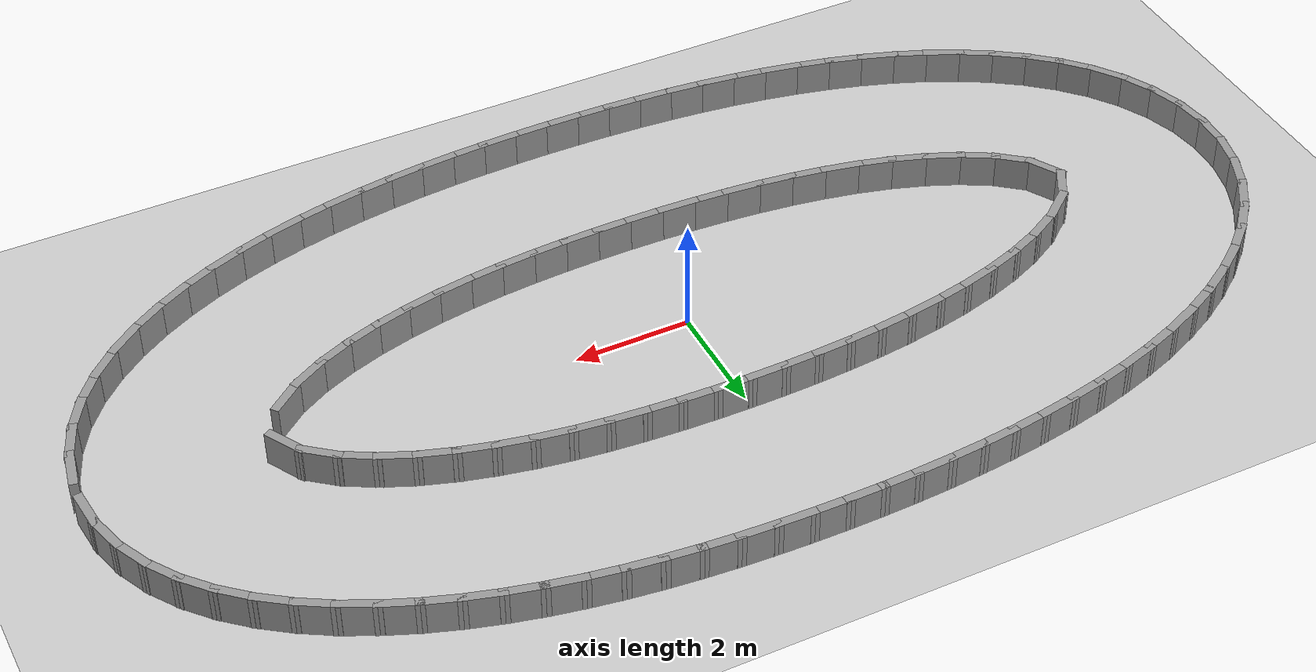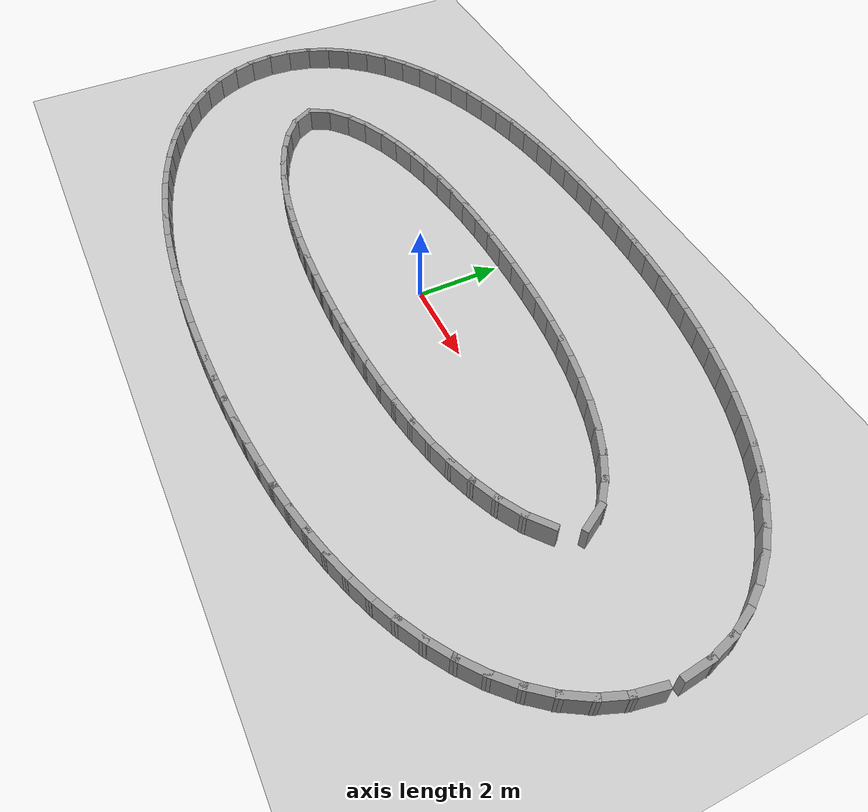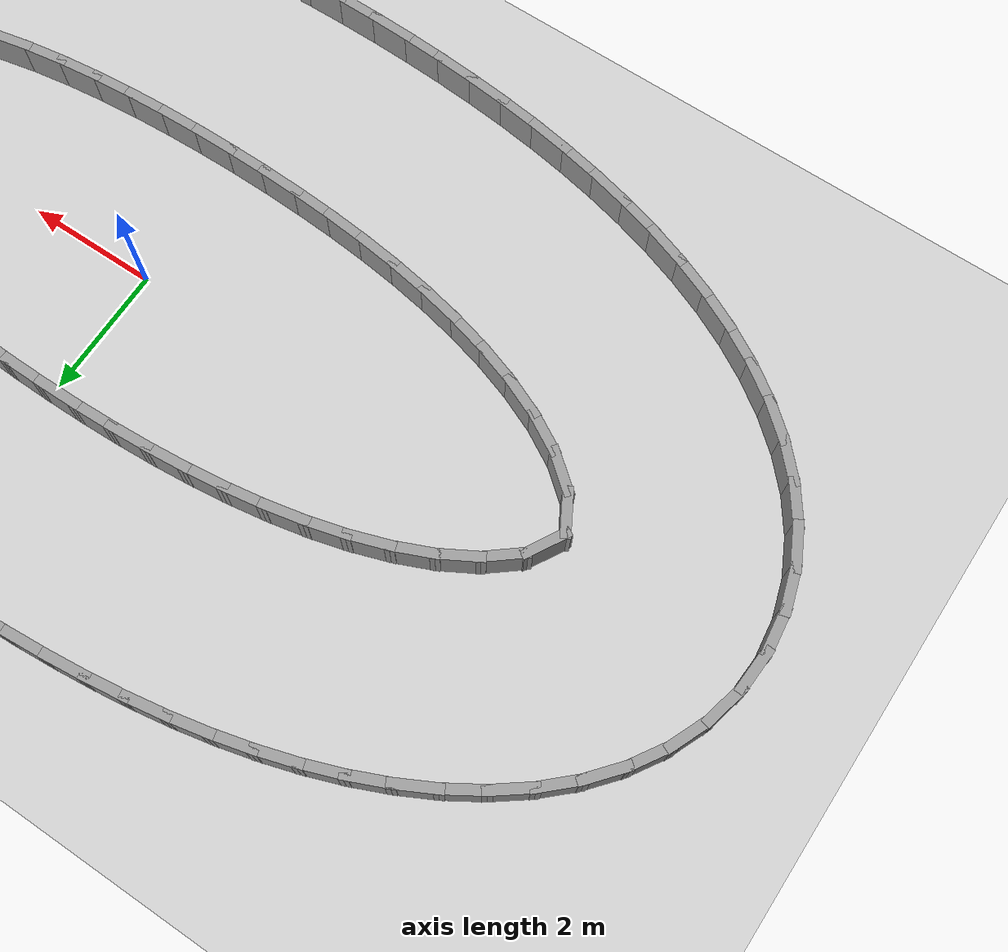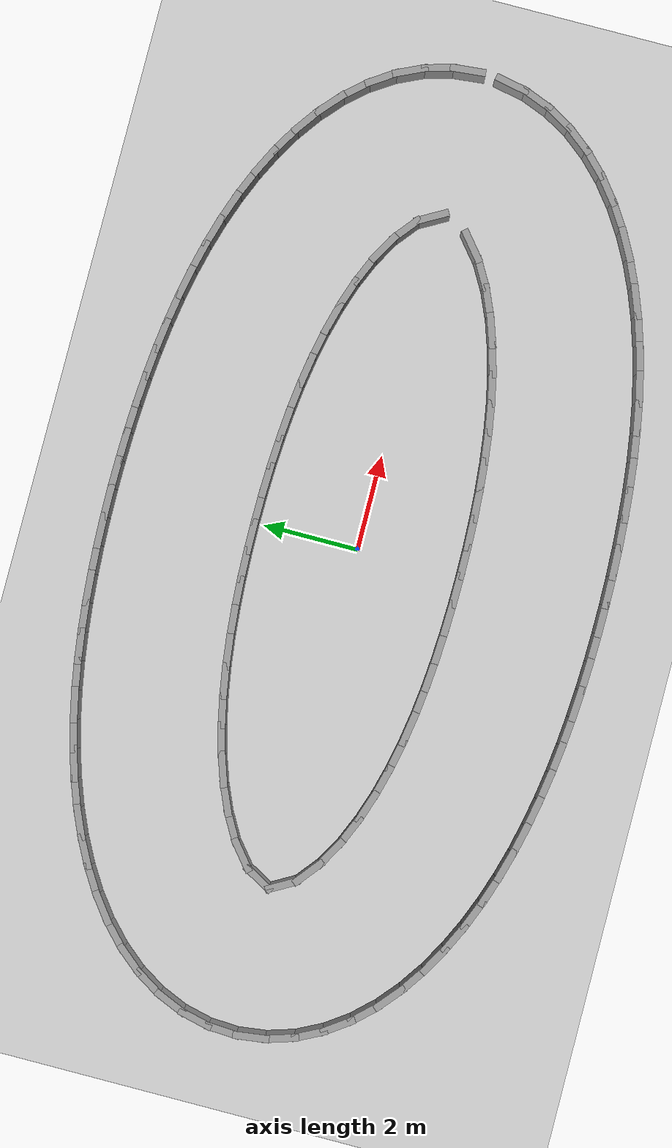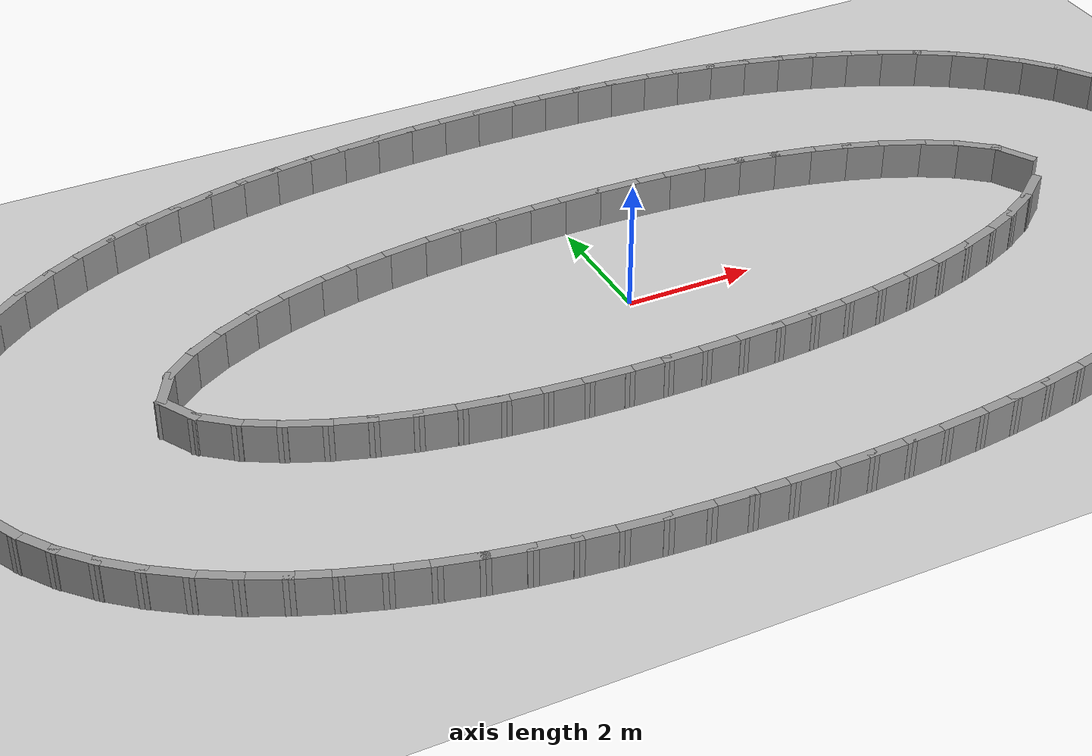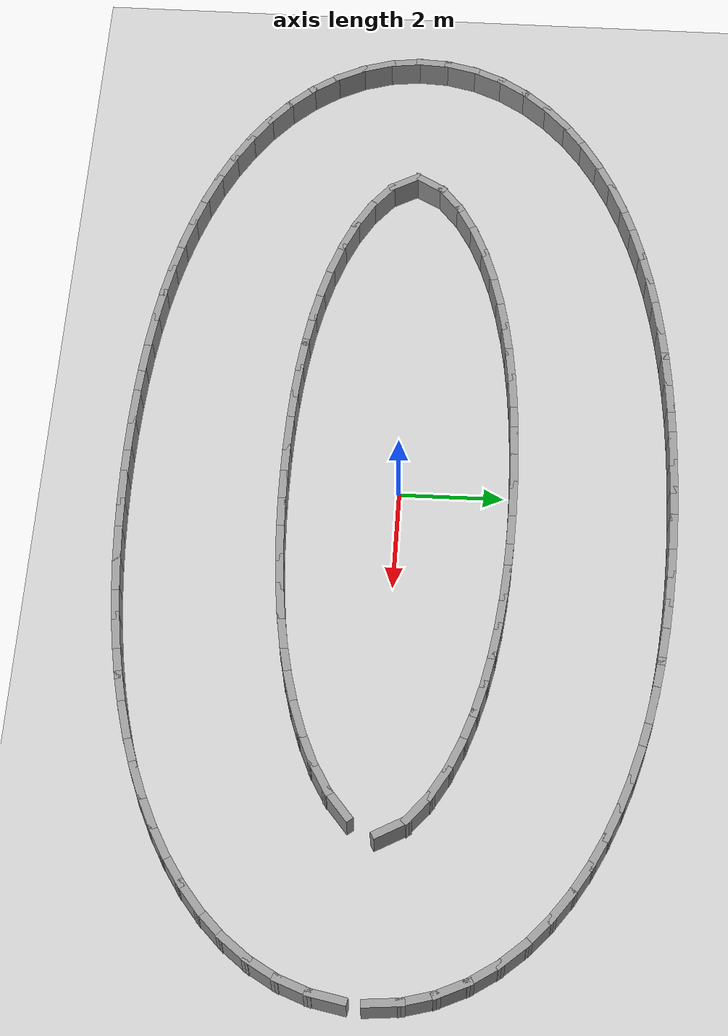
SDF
<?xml version="1.0" ?>
<sdf version='1.7'>
  <world name='default'>
    <plugin name='gazebo_ros_state' filename='libgazebo_ros_state.so'>
      <ros>
        <namespace>/</namespace>
      </ros>
      <update_rate>1000.0</update_rate>
    </plugin>

    <light name='sun' type='directional'>
      <cast_shadows>1</cast_shadows>
      <pose>0 0 10 0 -0 0</pose>
      <diffuse>0.8 0.8 0.8 1</diffuse>
      <specular>0.2 0.2 0.2 1</specular>
      <attenuation>
        <range>1000</range>
        <constant>0.9</constant>
        <linear>0.01</linear>
        <quadratic>0.001</quadratic>
      </attenuation>
      <direction>-0.5 0.1 -0.9</direction>
      <spot>
        <inner_angle>0</inner_angle>
        <outer_angle>0</outer_angle>
        <falloff>0</falloff>
      </spot>
    </light>
    <model name='ground_plane'>
      <static>1</static>
      <link name='link'>
        <collision name='collision'>
          <geometry>
            <plane>
              <normal>0 0 1</normal>
              <size>100 100</size>
            </plane>
          </geometry>
          <surface>
            <friction>
              <ode>
                <mu>100</mu>
                <mu2>50</mu2>
              </ode>
              <torsional>
                <ode/>
              </torsional>
            </friction>
            <contact>
              <ode/>
            </contact>
            <bounce/>
          </surface>
          <max_contacts>10</max_contacts>
        </collision>
        <visual name='visual'>
          <cast_shadows>0</cast_shadows>
          <geometry>
            <plane>
              <normal>0 0 1</normal>
              <size>100 100</size>
            </plane>
          </geometry>
          <material>
            <script>
              <uri>file://media/materials/scripts/gazebo.material</uri>
              <name>Gazebo/Grey</name>
            </script>
          </material>
        </visual>
        <self_collide>0</self_collide>
        <enable_wind>0</enable_wind>
        <kinematic>0</kinematic>
      </link>
    </model>
    <gravity>0 0 -9.8</gravity>
    <magnetic_field>6e-06 2.3e-05 -4.2e-05</magnetic_field>
    <atmosphere type='adiabatic'/>
    <physics type='ode'>
      <max_step_size>0.001</max_step_size>
      <real_time_factor>1</real_time_factor>
      <real_time_update_rate>1000</real_time_update_rate>
    </physics>
    <scene>
      <ambient>0.4 0.4 0.4 1</ambient>
      <background>0.7 0.7 0.7 1</background>
      <shadows>1</shadows>
    </scene>
    <audio>
      <device>default</device>
    </audio>
    <wind/>
    <spherical_coordinates>
      <surface_model>EARTH_WGS84</surface_model>
      <latitude_deg>0</latitude_deg>
      <longitude_deg>0</longitude_deg>
      <elevation>0</elevation>
      <heading_deg>0</heading_deg>
    </spherical_coordinates>
  <model name='rand_lobed_03'>
    <pose>0 0 0 0 -0 0</pose>
    <link name='Wall_0'>
      <collision name='Wall_0_Collision'>
        <geometry><box><size>0.7377 0.1500 0.6000</size></box></geometry>
        <pose>0 0 0.3000 0 -0 0</pose>
      </collision>
      <visual name='Wall_0_Visual'>
        <pose>0 0 0.3000 0 -0 0</pose>
        <geometry><box><size>0.7377 0.1500 0.6000</size></box></geometry>
        <material>
          <script>
            <uri>file://media/materials/scripts/gazebo.material</uri>
            <name>Gazebo/Grey</name>
          </script>
          <ambient>1 1 1 1</ambient>
        </material>
      </visual>
      <pose>6.9990 0.2561 0 0 -0 2.08328</pose>
    </link>
    <link name='Wall_1'>
      <collision name='Wall_1_Collision'>
        <geometry><box><size>0.7489 0.1500 0.6000</size></box></geometry>
        <pose>0 0 0.3000 0 -0 0</pose>
      </collision>
      <visual name='Wall_1_Visual'>
        <pose>0 0 0.3000 0 -0 0</pose>
        <geometry><box><size>0.7489 0.1500 0.6000</size></box></geometry>
        <material>
          <script>
            <uri>file://media/materials/scripts/gazebo.material</uri>
            <name>Gazebo/Grey</name>
          </script>
          <ambient>1 1 1 1</ambient>
        </material>
      </visual>
      <pose>6.6227 0.7012 0 0 -0 2.45838</pose>
    </link>
    <link name='Wall_2'>
      <collision name='Wall_2_Collision'>
        <geometry><box><size>0.7496 0.1500 0.6000</size></box></geometry>
        <pose>0 0 0.3000 0 -0 0</pose>
      </collision>
      <visual name='Wall_2_Visual'>
        <pose>0 0 0.3000 0 -0 0</pose>
        <geometry><box><size>0.7496 0.1500 0.6000</size></box></geometry>
        <material>
          <script>
            <uri>file://media/materials/scripts/gazebo.material</uri>
            <name>Gazebo/Grey</name>
          </script>
          <ambient>1 1 1 1</ambient>
        </material>
      </visual>
      <pose>6.1300 1.0386 0 0 -0 2.62367</pose>
    </link>
    <link name='Wall_3'>
      <collision name='Wall_3_Collision'>
        <geometry><box><size>0.7498 0.1500 0.6000</size></box></geometry>
        <pose>0 0 0.3000 0 -0 0</pose>
      </collision>
      <visual name='Wall_3_Visual'>
        <pose>0 0 0.3000 0 -0 0</pose>
        <geometry><box><size>0.7498 0.1500 0.6000</size></box></geometry>
        <material>
          <script>
            <uri>file://media/materials/scripts/gazebo.material</uri>
            <name>Gazebo/Grey</name>
          </script>
          <ambient>1 1 1 1</ambient>
        </material>
      </visual>
      <pose>5.5943 1.3062 0 0 -0 2.73311</pose>
    </link>
    <link name='Wall_4'>
      <collision name='Wall_4_Collision'>
        <geometry><box><size>0.7499 0.1500 0.6000</size></box></geometry>
        <pose>0 0 0.3000 0 -0 0</pose>
      </collision>
      <visual name='Wall_4_Visual'>
        <pose>0 0 0.3000 0 -0 0</pose>
        <geometry><box><size>0.7499 0.1500 0.6000</size></box></geometry>
        <material>
          <script>
            <uri>file://media/materials/scripts/gazebo.material</uri>
            <name>Gazebo/Grey</name>
          </script>
          <ambient>1 1 1 1</ambient>
        </material>
      </visual>
      <pose>5.0350 1.5214 0 0 -0 2.81528</pose>
    </link>
    <link name='Wall_5'>
      <collision name='Wall_5_Collision'>
        <geometry><box><size>0.7499 0.1500 0.6000</size></box></geometry>
        <pose>0 0 0.3000 0 -0 0</pose>
      </collision>
      <visual name='Wall_5_Visual'>
        <pose>0 0 0.3000 0 -0 0</pose>
        <geometry><box><size>0.7499 0.1500 0.6000</size></box></geometry>
        <material>
          <script>
            <uri>file://media/materials/scripts/gazebo.material</uri>
            <name>Gazebo/Grey</name>
          </script>
          <ambient>1 1 1 1</ambient>
        </material>
      </visual>
      <pose>4.4610 1.6948 0 0 -0 2.88108</pose>
    </link>
    <link name='Wall_6'>
      <collision name='Wall_6_Collision'>
        <geometry><box><size>0.7499 0.1500 0.6000</size></box></geometry>
        <pose>0 0 0.3000 0 -0 0</pose>
      </collision>
      <visual name='Wall_6_Visual'>
        <pose>0 0 0.3000 0 -0 0</pose>
        <geometry><box><size>0.7499 0.1500 0.6000</size></box></geometry>
        <material>
          <script>
            <uri>file://media/materials/scripts/gazebo.material</uri>
            <name>Gazebo/Grey</name>
          </script>
          <ambient>1 1 1 1</ambient>
        </material>
      </visual>
      <pose>3.8775 1.8334 0 0 -0 2.93567</pose>
    </link>
    <link name='Wall_7'>
      <collision name='Wall_7_Collision'>
        <geometry><box><size>0.7500 0.1500 0.6000</size></box></geometry>
        <pose>0 0 0.3000 0 -0 0</pose>
      </collision>
      <visual name='Wall_7_Visual'>
        <pose>0 0 0.3000 0 -0 0</pose>
        <geometry><box><size>0.7500 0.1500 0.6000</size></box></geometry>
        <material>
          <script>
            <uri>file://media/materials/scripts/gazebo.material</uri>
            <name>Gazebo/Grey</name>
          </script>
          <ambient>1 1 1 1</ambient>
        </material>
      </visual>
      <pose>3.2878 1.9425 0 0 -0 2.98180</pose>
    </link>
    <link name='Wall_8'>
      <collision name='Wall_8_Collision'>
        <geometry><box><size>0.7500 0.1500 0.6000</size></box></geometry>
        <pose>0 0 0.3000 0 -0 0</pose>
      </collision>
      <visual name='Wall_8_Visual'>
        <pose>0 0 0.3000 0 -0 0</pose>
        <geometry><box><size>0.7500 0.1500 0.6000</size></box></geometry>
        <material>
          <script>
            <uri>file://media/materials/scripts/gazebo.material</uri>
            <name>Gazebo/Grey</name>
          </script>
          <ambient>1 1 1 1</ambient>
        </material>
      </visual>
      <pose>2.6938 2.0263 0 0 -0 3.02109</pose>
    </link>
    <link name='Wall_9'>
      <collision name='Wall_9_Collision'>
        <geometry><box><size>0.7500 0.1500 0.6000</size></box></geometry>
        <pose>0 0 0.3000 0 -0 0</pose>
      </collision>
      <visual name='Wall_9_Visual'>
        <pose>0 0 0.3000 0 -0 0</pose>
        <geometry><box><size>0.7500 0.1500 0.6000</size></box></geometry>
        <material>
          <script>
            <uri>file://media/materials/scripts/gazebo.material</uri>
            <name>Gazebo/Grey</name>
          </script>
          <ambient>1 1 1 1</ambient>
        </material>
      </visual>
      <pose>2.0971 2.0884 0 0 -0 3.05462</pose>
    </link>
    <link name='Wall_10'>
      <collision name='Wall_10_Collision'>
        <geometry><box><size>0.7500 0.1500 0.6000</size></box></geometry>
        <pose>0 0 0.3000 0 -0 0</pose>
      </collision>
      <visual name='Wall_10_Visual'>
        <pose>0 0 0.3000 0 -0 0</pose>
        <geometry><box><size>0.7500 0.1500 0.6000</size></box></geometry>
        <material>
          <script>
            <uri>file://media/materials/scripts/gazebo.material</uri>
            <name>Gazebo/Grey</name>
          </script>
          <ambient>1 1 1 1</ambient>
        </material>
      </visual>
      <pose>1.4988 2.1319 0 0 -0 3.08334</pose>
    </link>
    <link name='Wall_11'>
      <collision name='Wall_11_Collision'>
        <geometry><box><size>0.7500 0.1500 0.6000</size></box></geometry>
        <pose>0 0 0.3000 0 -0 0</pose>
      </collision>
      <visual name='Wall_11_Visual'>
        <pose>0 0 0.3000 0 -0 0</pose>
        <geometry><box><size>0.7500 0.1500 0.6000</size></box></geometry>
        <material>
          <script>
            <uri>file://media/materials/scripts/gazebo.material</uri>
            <name>Gazebo/Grey</name>
          </script>
          <ambient>1 1 1 1</ambient>
        </material>
      </visual>
      <pose>0.8995 2.1594 0 0 -0 3.10828</pose>
    </link>
    <link name='Wall_12'>
      <collision name='Wall_12_Collision'>
        <geometry><box><size>0.7500 0.1500 0.6000</size></box></geometry>
        <pose>0 0 0.3000 0 -0 0</pose>
      </collision>
      <visual name='Wall_12_Visual'>
        <pose>0 0 0.3000 0 -0 0</pose>
        <geometry><box><size>0.7500 0.1500 0.6000</size></box></geometry>
        <material>
          <script>
            <uri>file://media/materials/scripts/gazebo.material</uri>
            <name>Gazebo/Grey</name>
          </script>
          <ambient>1 1 1 1</ambient>
        </material>
      </visual>
      <pose>0.2997 2.1726 0 0 -0 3.13078</pose>
    </link>
    <link name='Wall_13'>
      <collision name='Wall_13_Collision'>
        <geometry><box><size>0.7500 0.1500 0.6000</size></box></geometry>
        <pose>0 0 0.3000 0 -0 0</pose>
      </collision>
      <visual name='Wall_13_Visual'>
        <pose>0 0 0.3000 0 -0 0</pose>
        <geometry><box><size>0.7500 0.1500 0.6000</size></box></geometry>
        <material>
          <script>
            <uri>file://media/materials/scripts/gazebo.material</uri>
            <name>Gazebo/Grey</name>
          </script>
          <ambient>1 1 1 1</ambient>
        </material>
      </visual>
      <pose>-0.3003 2.1726 0 0 -0 -3.13076</pose>
    </link>
    <link name='Wall_14'>
      <collision name='Wall_14_Collision'>
        <geometry><box><size>0.7500 0.1500 0.6000</size></box></geometry>
        <pose>0 0 0.3000 0 -0 0</pose>
      </collision>
      <visual name='Wall_14_Visual'>
        <pose>0 0 0.3000 0 -0 0</pose>
        <geometry><box><size>0.7500 0.1500 0.6000</size></box></geometry>
        <material>
          <script>
            <uri>file://media/materials/scripts/gazebo.material</uri>
            <name>Gazebo/Grey</name>
          </script>
          <ambient>1 1 1 1</ambient>
        </material>
      </visual>
      <pose>-0.9001 2.1594 0 0 -0 -3.10826</pose>
    </link>
    <link name='Wall_15'>
      <collision name='Wall_15_Collision'>
        <geometry><box><size>0.7500 0.1500 0.6000</size></box></geometry>
        <pose>0 0 0.3000 0 -0 0</pose>
      </collision>
      <visual name='Wall_15_Visual'>
        <pose>0 0 0.3000 0 -0 0</pose>
        <geometry><box><size>0.7500 0.1500 0.6000</size></box></geometry>
        <material>
          <script>
            <uri>file://media/materials/scripts/gazebo.material</uri>
            <name>Gazebo/Grey</name>
          </script>
          <ambient>1 1 1 1</ambient>
        </material>
      </visual>
      <pose>-1.4994 2.1319 0 0 -0 -3.08331</pose>
    </link>
    <link name='Wall_16'>
      <collision name='Wall_16_Collision'>
        <geometry><box><size>0.7500 0.1500 0.6000</size></box></geometry>
        <pose>0 0 0.3000 0 -0 0</pose>
      </collision>
      <visual name='Wall_16_Visual'>
        <pose>0 0 0.3000 0 -0 0</pose>
        <geometry><box><size>0.7500 0.1500 0.6000</size></box></geometry>
        <material>
          <script>
            <uri>file://media/materials/scripts/gazebo.material</uri>
            <name>Gazebo/Grey</name>
          </script>
          <ambient>1 1 1 1</ambient>
        </material>
      </visual>
      <pose>-2.0977 2.0884 0 0 -0 -3.05459</pose>
    </link>
    <link name='Wall_17'>
      <collision name='Wall_17_Collision'>
        <geometry><box><size>0.7500 0.1500 0.6000</size></box></geometry>
        <pose>0 0 0.3000 0 -0 0</pose>
      </collision>
      <visual name='Wall_17_Visual'>
        <pose>0 0 0.3000 0 -0 0</pose>
        <geometry><box><size>0.7500 0.1500 0.6000</size></box></geometry>
        <material>
          <script>
            <uri>file://media/materials/scripts/gazebo.material</uri>
            <name>Gazebo/Grey</name>
          </script>
          <ambient>1 1 1 1</ambient>
        </material>
      </visual>
      <pose>-2.6944 2.0262 0 0 -0 -3.02105</pose>
    </link>
    <link name='Wall_18'>
      <collision name='Wall_18_Collision'>
        <geometry><box><size>0.7500 0.1500 0.6000</size></box></geometry>
        <pose>0 0 0.3000 0 -0 0</pose>
      </collision>
      <visual name='Wall_18_Visual'>
        <pose>0 0 0.3000 0 -0 0</pose>
        <geometry><box><size>0.7500 0.1500 0.6000</size></box></geometry>
        <material>
          <script>
            <uri>file://media/materials/scripts/gazebo.material</uri>
            <name>Gazebo/Grey</name>
          </script>
          <ambient>1 1 1 1</ambient>
        </material>
      </visual>
      <pose>-3.2883 1.9424 0 0 -0 -2.98176</pose>
    </link>
    <link name='Wall_19'>
      <collision name='Wall_19_Collision'>
        <geometry><box><size>0.7499 0.1500 0.6000</size></box></geometry>
        <pose>0 0 0.3000 0 -0 0</pose>
      </collision>
      <visual name='Wall_19_Visual'>
        <pose>0 0 0.3000 0 -0 0</pose>
        <geometry><box><size>0.7499 0.1500 0.6000</size></box></geometry>
        <material>
          <script>
            <uri>file://media/materials/scripts/gazebo.material</uri>
            <name>Gazebo/Grey</name>
          </script>
          <ambient>1 1 1 1</ambient>
        </material>
      </visual>
      <pose>-3.8781 1.8333 0 0 -0 -2.93562</pose>
    </link>
    <link name='Wall_20'>
      <collision name='Wall_20_Collision'>
        <geometry><box><size>0.7499 0.1500 0.6000</size></box></geometry>
        <pose>0 0 0.3000 0 -0 0</pose>
      </collision>
      <visual name='Wall_20_Visual'>
        <pose>0 0 0.3000 0 -0 0</pose>
        <geometry><box><size>0.7499 0.1500 0.6000</size></box></geometry>
        <material>
          <script>
            <uri>file://media/materials/scripts/gazebo.material</uri>
            <name>Gazebo/Grey</name>
          </script>
          <ambient>1 1 1 1</ambient>
        </material>
      </visual>
      <pose>-4.4616 1.6947 0 0 -0 -2.88102</pose>
    </link>
    <link name='Wall_21'>
      <collision name='Wall_21_Collision'>
        <geometry><box><size>0.7499 0.1500 0.6000</size></box></geometry>
        <pose>0 0 0.3000 0 -0 0</pose>
      </collision>
      <visual name='Wall_21_Visual'>
        <pose>0 0 0.3000 0 -0 0</pose>
        <geometry><box><size>0.7499 0.1500 0.6000</size></box></geometry>
        <material>
          <script>
            <uri>file://media/materials/scripts/gazebo.material</uri>
            <name>Gazebo/Grey</name>
          </script>
          <ambient>1 1 1 1</ambient>
        </material>
      </visual>
      <pose>-5.0355 1.5213 0 0 -0 -2.81521</pose>
    </link>
    <link name='Wall_22'>
      <collision name='Wall_22_Collision'>
        <geometry><box><size>0.7498 0.1500 0.6000</size></box></geometry>
        <pose>0 0 0.3000 0 -0 0</pose>
      </collision>
      <visual name='Wall_22_Visual'>
        <pose>0 0 0.3000 0 -0 0</pose>
        <geometry><box><size>0.7498 0.1500 0.6000</size></box></geometry>
        <material>
          <script>
            <uri>file://media/materials/scripts/gazebo.material</uri>
            <name>Gazebo/Grey</name>
          </script>
          <ambient>1 1 1 1</ambient>
        </material>
      </visual>
      <pose>-5.5948 1.3059 0 0 -0 -2.73302</pose>
    </link>
    <link name='Wall_23'>
      <collision name='Wall_23_Collision'>
        <geometry><box><size>0.7496 0.1500 0.6000</size></box></geometry>
        <pose>0 0 0.3000 0 -0 0</pose>
      </collision>
      <visual name='Wall_23_Visual'>
        <pose>0 0 0.3000 0 -0 0</pose>
        <geometry><box><size>0.7496 0.1500 0.6000</size></box></geometry>
        <material>
          <script>
            <uri>file://media/materials/scripts/gazebo.material</uri>
            <name>Gazebo/Grey</name>
          </script>
          <ambient>1 1 1 1</ambient>
        </material>
      </visual>
      <pose>-6.1305 1.0383 0 0 -0 -2.62355</pose>
    </link>
    <link name='Wall_24'>
      <collision name='Wall_24_Collision'>
        <geometry><box><size>0.7489 0.1500 0.6000</size></box></geometry>
        <pose>0 0 0.3000 0 -0 0</pose>
      </collision>
      <visual name='Wall_24_Visual'>
        <pose>0 0 0.3000 0 -0 0</pose>
        <geometry><box><size>0.7489 0.1500 0.6000</size></box></geometry>
        <material>
          <script>
            <uri>file://media/materials/scripts/gazebo.material</uri>
            <name>Gazebo/Grey</name>
          </script>
          <ambient>1 1 1 1</ambient>
        </material>
      </visual>
      <pose>-6.6231 0.7008 0 0 -0 -2.45816</pose>
    </link>
    <link name='Wall_25'>
      <collision name='Wall_25_Collision'>
        <geometry><box><size>0.7376 0.1500 0.6000</size></box></geometry>
        <pose>0 0 0.3000 0 -0 0</pose>
      </collision>
      <visual name='Wall_25_Visual'>
        <pose>0 0 0.3000 0 -0 0</pose>
        <geometry><box><size>0.7376 0.1500 0.6000</size></box></geometry>
        <material>
          <script>
            <uri>file://media/materials/scripts/gazebo.material</uri>
            <name>Gazebo/Grey</name>
          </script>
          <ambient>1 1 1 1</ambient>
        </material>
      </visual>
      <pose>-6.9992 0.2556 0 0 -0 -2.08253</pose>
    </link>
    <link name='Wall_26'>
      <collision name='Wall_26_Collision'>
        <geometry><box><size>0.7377 0.1500 0.6000</size></box></geometry>
        <pose>0 0 0.3000 0 -0 0</pose>
      </collision>
      <visual name='Wall_26_Visual'>
        <pose>0 0 0.3000 0 -0 0</pose>
        <geometry><box><size>0.7377 0.1500 0.6000</size></box></geometry>
        <material>
          <script>
            <uri>file://media/materials/scripts/gazebo.material</uri>
            <name>Gazebo/Grey</name>
          </script>
          <ambient>1 1 1 1</ambient>
        </material>
      </visual>
      <pose>-6.9988 -0.2566 0 0 -0 -1.05758</pose>
    </link>
    <link name='Wall_27'>
      <collision name='Wall_27_Collision'>
        <geometry><box><size>0.7489 0.1500 0.6000</size></box></geometry>
        <pose>0 0 0.3000 0 -0 0</pose>
      </collision>
      <visual name='Wall_27_Visual'>
        <pose>0 0 0.3000 0 -0 0</pose>
        <geometry><box><size>0.7489 0.1500 0.6000</size></box></geometry>
        <material>
          <script>
            <uri>file://media/materials/scripts/gazebo.material</uri>
            <name>Gazebo/Grey</name>
          </script>
          <ambient>1 1 1 1</ambient>
        </material>
      </visual>
      <pose>-6.6222 -0.7016 0 0 -0 -0.68301</pose>
    </link>
    <link name='Wall_28'>
      <collision name='Wall_28_Collision'>
        <geometry><box><size>0.7496 0.1500 0.6000</size></box></geometry>
        <pose>0 0 0.3000 0 -0 0</pose>
      </collision>
      <visual name='Wall_28_Visual'>
        <pose>0 0 0.3000 0 -0 0</pose>
        <geometry><box><size>0.7496 0.1500 0.6000</size></box></geometry>
        <material>
          <script>
            <uri>file://media/materials/scripts/gazebo.material</uri>
            <name>Gazebo/Grey</name>
          </script>
          <ambient>1 1 1 1</ambient>
        </material>
      </visual>
      <pose>-6.1295 -1.0389 0 0 -0 -0.51780</pose>
    </link>
    <link name='Wall_29'>
      <collision name='Wall_29_Collision'>
        <geometry><box><size>0.7498 0.1500 0.6000</size></box></geometry>
        <pose>0 0 0.3000 0 -0 0</pose>
      </collision>
      <visual name='Wall_29_Visual'>
        <pose>0 0 0.3000 0 -0 0</pose>
        <geometry><box><size>0.7498 0.1500 0.6000</size></box></geometry>
        <material>
          <script>
            <uri>file://media/materials/scripts/gazebo.material</uri>
            <name>Gazebo/Grey</name>
          </script>
          <ambient>1 1 1 1</ambient>
        </material>
      </visual>
      <pose>-5.5937 -1.3064 0 0 -0 -0.40839</pose>
    </link>
    <link name='Wall_30'>
      <collision name='Wall_30_Collision'>
        <geometry><box><size>0.7499 0.1500 0.6000</size></box></geometry>
        <pose>0 0 0.3000 0 -0 0</pose>
      </collision>
      <visual name='Wall_30_Visual'>
        <pose>0 0 0.3000 0 -0 0</pose>
        <geometry><box><size>0.7499 0.1500 0.6000</size></box></geometry>
        <material>
          <script>
            <uri>file://media/materials/scripts/gazebo.material</uri>
            <name>Gazebo/Grey</name>
          </script>
          <ambient>1 1 1 1</ambient>
        </material>
      </visual>
      <pose>-5.0344 -1.5216 0 0 -0 -0.32624</pose>
    </link>
    <link name='Wall_31'>
      <collision name='Wall_31_Collision'>
        <geometry><box><size>0.7499 0.1500 0.6000</size></box></geometry>
        <pose>0 0 0.3000 0 -0 0</pose>
      </collision>
      <visual name='Wall_31_Visual'>
        <pose>0 0 0.3000 0 -0 0</pose>
        <geometry><box><size>0.7499 0.1500 0.6000</size></box></geometry>
        <material>
          <script>
            <uri>file://media/materials/scripts/gazebo.material</uri>
            <name>Gazebo/Grey</name>
          </script>
          <ambient>1 1 1 1</ambient>
        </material>
      </visual>
      <pose>-4.4604 -1.6950 0 0 -0 -0.26045</pose>
    </link>
    <link name='Wall_32'>
      <collision name='Wall_32_Collision'>
        <geometry><box><size>0.7499 0.1500 0.6000</size></box></geometry>
        <pose>0 0 0.3000 0 -0 0</pose>
      </collision>
      <visual name='Wall_32_Visual'>
        <pose>0 0 0.3000 0 -0 0</pose>
        <geometry><box><size>0.7499 0.1500 0.6000</size></box></geometry>
        <material>
          <script>
            <uri>file://media/materials/scripts/gazebo.material</uri>
            <name>Gazebo/Grey</name>
          </script>
          <ambient>1 1 1 1</ambient>
        </material>
      </visual>
      <pose>-3.8770 -1.8336 0 0 -0 -0.20588</pose>
    </link>
    <link name='Wall_33'>
      <collision name='Wall_33_Collision'>
        <geometry><box><size>0.7500 0.1500 0.6000</size></box></geometry>
        <pose>0 0 0.3000 0 -0 0</pose>
      </collision>
      <visual name='Wall_33_Visual'>
        <pose>0 0 0.3000 0 -0 0</pose>
        <geometry><box><size>0.7500 0.1500 0.6000</size></box></geometry>
        <material>
          <script>
            <uri>file://media/materials/scripts/gazebo.material</uri>
            <name>Gazebo/Grey</name>
          </script>
          <ambient>1 1 1 1</ambient>
        </material>
      </visual>
      <pose>-3.2872 -1.9426 0 0 -0 -0.15975</pose>
    </link>
    <link name='Wall_34'>
      <collision name='Wall_34_Collision'>
        <geometry><box><size>0.7500 0.1500 0.6000</size></box></geometry>
        <pose>0 0 0.3000 0 -0 0</pose>
      </collision>
      <visual name='Wall_34_Visual'>
        <pose>0 0 0.3000 0 -0 0</pose>
        <geometry><box><size>0.7500 0.1500 0.6000</size></box></geometry>
        <material>
          <script>
            <uri>file://media/materials/scripts/gazebo.material</uri>
            <name>Gazebo/Grey</name>
          </script>
          <ambient>1 1 1 1</ambient>
        </material>
      </visual>
      <pose>-2.6932 -2.0264 0 0 -0 -0.12047</pose>
    </link>
    <link name='Wall_35'>
      <collision name='Wall_35_Collision'>
        <geometry><box><size>0.7500 0.1500 0.6000</size></box></geometry>
        <pose>0 0 0.3000 0 -0 0</pose>
      </collision>
      <visual name='Wall_35_Visual'>
        <pose>0 0 0.3000 0 -0 0</pose>
        <geometry><box><size>0.7500 0.1500 0.6000</size></box></geometry>
        <material>
          <script>
            <uri>file://media/materials/scripts/gazebo.material</uri>
            <name>Gazebo/Grey</name>
          </script>
          <ambient>1 1 1 1</ambient>
        </material>
      </visual>
      <pose>-2.0966 -2.0885 0 0 -0 -0.08694</pose>
    </link>
    <link name='Wall_36'>
      <collision name='Wall_36_Collision'>
        <geometry><box><size>0.7500 0.1500 0.6000</size></box></geometry>
        <pose>0 0 0.3000 0 -0 0</pose>
      </collision>
      <visual name='Wall_36_Visual'>
        <pose>0 0 0.3000 0 -0 0</pose>
        <geometry><box><size>0.7500 0.1500 0.6000</size></box></geometry>
        <material>
          <script>
            <uri>file://media/materials/scripts/gazebo.material</uri>
            <name>Gazebo/Grey</name>
          </script>
          <ambient>1 1 1 1</ambient>
        </material>
      </visual>
      <pose>-1.4982 -2.1320 0 0 -0 -0.05823</pose>
    </link>
    <link name='Wall_37'>
      <collision name='Wall_37_Collision'>
        <geometry><box><size>0.7500 0.1500 0.6000</size></box></geometry>
        <pose>0 0 0.3000 0 -0 0</pose>
      </collision>
      <visual name='Wall_37_Visual'>
        <pose>0 0 0.3000 0 -0 0</pose>
        <geometry><box><size>0.7500 0.1500 0.6000</size></box></geometry>
        <material>
          <script>
            <uri>file://media/materials/scripts/gazebo.material</uri>
            <name>Gazebo/Grey</name>
          </script>
          <ambient>1 1 1 1</ambient>
        </material>
      </visual>
      <pose>-0.8989 -2.1594 0 0 -0 -0.03329</pose>
    </link>
    <link name='Wall_38'>
      <collision name='Wall_38_Collision'>
        <geometry><box><size>0.7500 0.1500 0.6000</size></box></geometry>
        <pose>0 0 0.3000 0 -0 0</pose>
      </collision>
      <visual name='Wall_38_Visual'>
        <pose>0 0 0.3000 0 -0 0</pose>
        <geometry><box><size>0.7500 0.1500 0.6000</size></box></geometry>
        <material>
          <script>
            <uri>file://media/materials/scripts/gazebo.material</uri>
            <name>Gazebo/Grey</name>
          </script>
          <ambient>1 1 1 1</ambient>
        </material>
      </visual>
      <pose>-0.2991 -2.1726 0 0 -0 -0.01079</pose>
    </link>
    <link name='Wall_39'>
      <collision name='Wall_39_Collision'>
        <geometry><box><size>0.7500 0.1500 0.6000</size></box></geometry>
        <pose>0 0 0.3000 0 -0 0</pose>
      </collision>
      <visual name='Wall_39_Visual'>
        <pose>0 0 0.3000 0 -0 0</pose>
        <geometry><box><size>0.7500 0.1500 0.6000</size></box></geometry>
        <material>
          <script>
            <uri>file://media/materials/scripts/gazebo.material</uri>
            <name>Gazebo/Grey</name>
          </script>
          <ambient>1 1 1 1</ambient>
        </material>
      </visual>
      <pose>0.3009 -2.1726 0 0 -0 0.01086</pose>
    </link>
    <link name='Wall_40'>
      <collision name='Wall_40_Collision'>
        <geometry><box><size>0.7500 0.1500 0.6000</size></box></geometry>
        <pose>0 0 0.3000 0 -0 0</pose>
      </collision>
      <visual name='Wall_40_Visual'>
        <pose>0 0 0.3000 0 -0 0</pose>
        <geometry><box><size>0.7500 0.1500 0.6000</size></box></geometry>
        <material>
          <script>
            <uri>file://media/materials/scripts/gazebo.material</uri>
            <name>Gazebo/Grey</name>
          </script>
          <ambient>1 1 1 1</ambient>
        </material>
      </visual>
      <pose>0.9007 -2.1594 0 0 -0 0.03336</pose>
    </link>
    <link name='Wall_41'>
      <collision name='Wall_41_Collision'>
        <geometry><box><size>0.7500 0.1500 0.6000</size></box></geometry>
        <pose>0 0 0.3000 0 -0 0</pose>
      </collision>
      <visual name='Wall_41_Visual'>
        <pose>0 0 0.3000 0 -0 0</pose>
        <geometry><box><size>0.7500 0.1500 0.6000</size></box></geometry>
        <material>
          <script>
            <uri>file://media/materials/scripts/gazebo.material</uri>
            <name>Gazebo/Grey</name>
          </script>
          <ambient>1 1 1 1</ambient>
        </material>
      </visual>
      <pose>1.5000 -2.1319 0 0 -0 0.05830</pose>
    </link>
    <link name='Wall_42'>
      <collision name='Wall_42_Collision'>
        <geometry><box><size>0.7500 0.1500 0.6000</size></box></geometry>
        <pose>0 0 0.3000 0 -0 0</pose>
      </collision>
      <visual name='Wall_42_Visual'>
        <pose>0 0 0.3000 0 -0 0</pose>
        <geometry><box><size>0.7500 0.1500 0.6000</size></box></geometry>
        <material>
          <script>
            <uri>file://media/materials/scripts/gazebo.material</uri>
            <name>Gazebo/Grey</name>
          </script>
          <ambient>1 1 1 1</ambient>
        </material>
      </visual>
      <pose>2.0983 -2.0883 0 0 -0 0.08703</pose>
    </link>
    <link name='Wall_43'>
      <collision name='Wall_43_Collision'>
        <geometry><box><size>0.7500 0.1500 0.6000</size></box></geometry>
        <pose>0 0 0.3000 0 -0 0</pose>
      </collision>
      <visual name='Wall_43_Visual'>
        <pose>0 0 0.3000 0 -0 0</pose>
        <geometry><box><size>0.7500 0.1500 0.6000</size></box></geometry>
        <material>
          <script>
            <uri>file://media/materials/scripts/gazebo.material</uri>
            <name>Gazebo/Grey</name>
          </script>
          <ambient>1 1 1 1</ambient>
        </material>
      </visual>
      <pose>2.6950 -2.0262 0 0 -0 0.12058</pose>
    </link>
    <link name='Wall_44'>
      <collision name='Wall_44_Collision'>
        <geometry><box><size>0.7500 0.1500 0.6000</size></box></geometry>
        <pose>0 0 0.3000 0 -0 0</pose>
      </collision>
      <visual name='Wall_44_Visual'>
        <pose>0 0 0.3000 0 -0 0</pose>
        <geometry><box><size>0.7500 0.1500 0.6000</size></box></geometry>
        <material>
          <script>
            <uri>file://media/materials/scripts/gazebo.material</uri>
            <name>Gazebo/Grey</name>
          </script>
          <ambient>1 1 1 1</ambient>
        </material>
      </visual>
      <pose>3.2889 -1.9423 0 0 -0 0.15987</pose>
    </link>
    <link name='Wall_45'>
      <collision name='Wall_45_Collision'>
        <geometry><box><size>0.7499 0.1500 0.6000</size></box></geometry>
        <pose>0 0 0.3000 0 -0 0</pose>
      </collision>
      <visual name='Wall_45_Visual'>
        <pose>0 0 0.3000 0 -0 0</pose>
        <geometry><box><size>0.7499 0.1500 0.6000</size></box></geometry>
        <material>
          <script>
            <uri>file://media/materials/scripts/gazebo.material</uri>
            <name>Gazebo/Grey</name>
          </script>
          <ambient>1 1 1 1</ambient>
        </material>
      </visual>
      <pose>3.8787 -1.8332 0 0 -0 0.20602</pose>
    </link>
    <link name='Wall_46'>
      <collision name='Wall_46_Collision'>
        <geometry><box><size>0.7499 0.1500 0.6000</size></box></geometry>
        <pose>0 0 0.3000 0 -0 0</pose>
      </collision>
      <visual name='Wall_46_Visual'>
        <pose>0 0 0.3000 0 -0 0</pose>
        <geometry><box><size>0.7499 0.1500 0.6000</size></box></geometry>
        <material>
          <script>
            <uri>file://media/materials/scripts/gazebo.material</uri>
            <name>Gazebo/Grey</name>
          </script>
          <ambient>1 1 1 1</ambient>
        </material>
      </visual>
      <pose>4.4621 -1.6945 0 0 -0 0.26063</pose>
    </link>
    <link name='Wall_47'>
      <collision name='Wall_47_Collision'>
        <geometry><box><size>0.7499 0.1500 0.6000</size></box></geometry>
        <pose>0 0 0.3000 0 -0 0</pose>
      </collision>
      <visual name='Wall_47_Visual'>
        <pose>0 0 0.3000 0 -0 0</pose>
        <geometry><box><size>0.7499 0.1500 0.6000</size></box></geometry>
        <material>
          <script>
            <uri>file://media/materials/scripts/gazebo.material</uri>
            <name>Gazebo/Grey</name>
          </script>
          <ambient>1 1 1 1</ambient>
        </material>
      </visual>
      <pose>5.0361 -1.5211 0 0 -0 0.32645</pose>
    </link>
    <link name='Wall_48'>
      <collision name='Wall_48_Collision'>
        <geometry><box><size>0.7498 0.1500 0.6000</size></box></geometry>
        <pose>0 0 0.3000 0 -0 0</pose>
      </collision>
      <visual name='Wall_48_Visual'>
        <pose>0 0 0.3000 0 -0 0</pose>
        <geometry><box><size>0.7498 0.1500 0.6000</size></box></geometry>
        <material>
          <script>
            <uri>file://media/materials/scripts/gazebo.material</uri>
            <name>Gazebo/Grey</name>
          </script>
          <ambient>1 1 1 1</ambient>
        </material>
      </visual>
      <pose>5.5953 -1.3057 0 0 -0 0.40866</pose>
    </link>
    <link name='Wall_49'>
      <collision name='Wall_49_Collision'>
        <geometry><box><size>0.7496 0.1500 0.6000</size></box></geometry>
        <pose>0 0 0.3000 0 -0 0</pose>
      </collision>
      <visual name='Wall_49_Visual'>
        <pose>0 0 0.3000 0 -0 0</pose>
        <geometry><box><size>0.7496 0.1500 0.6000</size></box></geometry>
        <material>
          <script>
            <uri>file://media/materials/scripts/gazebo.material</uri>
            <name>Gazebo/Grey</name>
          </script>
          <ambient>1 1 1 1</ambient>
        </material>
      </visual>
      <pose>6.1310 -1.0381 0 0 -0 0.51816</pose>
    </link>
    <link name='Wall_50'>
      <collision name='Wall_50_Collision'>
        <geometry><box><size>0.7489 0.1500 0.6000</size></box></geometry>
        <pose>0 0 0.3000 0 -0 0</pose>
      </collision>
      <visual name='Wall_50_Visual'>
        <pose>0 0 0.3000 0 -0 0</pose>
        <geometry><box><size>0.7489 0.1500 0.6000</size></box></geometry>
        <material>
          <script>
            <uri>file://media/materials/scripts/gazebo.material</uri>
            <name>Gazebo/Grey</name>
          </script>
          <ambient>1 1 1 1</ambient>
        </material>
      </visual>
      <pose>6.6236 -0.7004 0 0 -0 0.68364</pose>
    </link>
    <link name='Wall_51'>
      <collision name='Wall_51_Collision'>
        <geometry><box><size>0.7492 0.1500 0.6000</size></box></geometry>
        <pose>0 0 0.3000 0 -0 0</pose>
      </collision>
      <visual name='Wall_51_Visual'>
        <pose>0 0 0.3000 0 -0 0</pose>
        <geometry><box><size>0.7492 0.1500 0.6000</size></box></geometry>
        <material>
          <script>
            <uri>file://media/materials/scripts/gazebo.material</uri>
            <name>Gazebo/Grey</name>
          </script>
          <ambient>1 1 1 1</ambient>
        </material>
      </visual>
      <pose>10.1354 0.2984 0 0 -0 1.66104</pose>
    </link>
    <link name='Wall_52'>
      <collision name='Wall_52_Collision'>
        <geometry><box><size>0.7492 0.1500 0.6000</size></box></geometry>
        <pose>0 0 0.3000 0 -0 0</pose>
      </collision>
      <visual name='Wall_52_Visual'>
        <pose>0 0 0.3000 0 -0 0</pose>
        <geometry><box><size>0.7492 0.1500 0.6000</size></box></geometry>
        <material>
          <script>
            <uri>file://media/materials/scripts/gazebo.material</uri>
            <name>Gazebo/Grey</name>
          </script>
          <ambient>1 1 1 1</ambient>
        </material>
      </visual>
      <pose>10.0294 0.8858 0 0 -0 1.83783</pose>
    </link>
    <link name='Wall_53'>
      <collision name='Wall_53_Collision'>
        <geometry><box><size>0.7494 0.1500 0.6000</size></box></geometry>
        <pose>0 0 0.3000 0 -0 0</pose>
      </collision>
      <visual name='Wall_53_Visual'>
        <pose>0 0 0.3000 0 -0 0</pose>
        <geometry><box><size>0.7494 0.1500 0.6000</size></box></geometry>
        <material>
          <script>
            <uri>file://media/materials/scripts/gazebo.material</uri>
            <name>Gazebo/Grey</name>
          </script>
          <ambient>1 1 1 1</ambient>
        </material>
      </visual>
      <pose>9.8242 1.4466 0 0 -0 2.00498</pose>
    </link>
    <link name='Wall_54'>
      <collision name='Wall_54_Collision'>
        <geometry><box><size>0.7495 0.1500 0.6000</size></box></geometry>
        <pose>0 0 0.3000 0 -0 0</pose>
      </collision>
      <visual name='Wall_54_Visual'>
        <pose>0 0 0.3000 0 -0 0</pose>
        <geometry><box><size>0.7495 0.1500 0.6000</size></box></geometry>
        <material>
          <script>
            <uri>file://media/materials/scripts/gazebo.material</uri>
            <name>Gazebo/Grey</name>
          </script>
          <ambient>1 1 1 1</ambient>
        </material>
      </visual>
      <pose>9.5322 1.9681 0 0 -0 2.15755</pose>
    </link>
    <link name='Wall_55'>
      <collision name='Wall_55_Collision'>
        <geometry><box><size>0.7496 0.1500 0.6000</size></box></geometry>
        <pose>0 0 0.3000 0 -0 0</pose>
      </collision>
      <visual name='Wall_55_Visual'>
        <pose>0 0 0.3000 0 -0 0</pose>
        <geometry><box><size>0.7496 0.1500 0.6000</size></box></geometry>
        <material>
          <script>
            <uri>file://media/materials/scripts/gazebo.material</uri>
            <name>Gazebo/Grey</name>
          </script>
          <ambient>1 1 1 1</ambient>
        </material>
      </visual>
      <pose>9.1681 2.4427 0 0 -0 2.29304</pose>
    </link>
    <link name='Wall_56'>
      <collision name='Wall_56_Collision'>
        <geometry><box><size>0.7497 0.1500 0.6000</size></box></geometry>
        <pose>0 0 0.3000 0 -0 0</pose>
      </collision>
      <visual name='Wall_56_Visual'>
        <pose>0 0 0.3000 0 -0 0</pose>
        <geometry><box><size>0.7497 0.1500 0.6000</size></box></geometry>
        <material>
          <script>
            <uri>file://media/materials/scripts/gazebo.material</uri>
            <name>Gazebo/Grey</name>
          </script>
          <ambient>1 1 1 1</ambient>
        </material>
      </visual>
      <pose>8.7466 2.8677 0 0 -0 2.41105</pose>
    </link>
    <link name='Wall_57'>
      <collision name='Wall_57_Collision'>
        <geometry><box><size>0.7498 0.1500 0.6000</size></box></geometry>
        <pose>0 0 0.3000 0 -0 0</pose>
      </collision>
      <visual name='Wall_57_Visual'>
        <pose>0 0 0.3000 0 -0 0</pose>
        <geometry><box><size>0.7498 0.1500 0.6000</size></box></geometry>
        <material>
          <script>
            <uri>file://media/materials/scripts/gazebo.material</uri>
            <name>Gazebo/Grey</name>
          </script>
          <ambient>1 1 1 1</ambient>
        </material>
      </visual>
      <pose>8.2807 3.2441 0 0 -0 2.51288</pose>
    </link>
    <link name='Wall_58'>
      <collision name='Wall_58_Collision'>
        <geometry><box><size>0.7498 0.1500 0.6000</size></box></geometry>
        <pose>0 0 0.3000 0 -0 0</pose>
      </collision>
      <visual name='Wall_58_Visual'>
        <pose>0 0 0.3000 0 -0 0</pose>
        <geometry><box><size>0.7498 0.1500 0.6000</size></box></geometry>
        <material>
          <script>
            <uri>file://media/materials/scripts/gazebo.material</uri>
            <name>Gazebo/Grey</name>
          </script>
          <ambient>1 1 1 1</ambient>
        </material>
      </visual>
      <pose>7.7810 3.5749 0 0 -0 2.60069</pose>
    </link>
    <link name='Wall_59'>
      <collision name='Wall_59_Collision'>
        <geometry><box><size>0.7499 0.1500 0.6000</size></box></geometry>
        <pose>0 0 0.3000 0 -0 0</pose>
      </collision>
      <visual name='Wall_59_Visual'>
        <pose>0 0 0.3000 0 -0 0</pose>
        <geometry><box><size>0.7499 0.1500 0.6000</size></box></geometry>
        <material>
          <script>
            <uri>file://media/materials/scripts/gazebo.material</uri>
            <name>Gazebo/Grey</name>
          </script>
          <ambient>1 1 1 1</ambient>
        </material>
      </visual>
      <pose>7.2558 3.8638 0 0 -0 2.67666</pose>
    </link>
    <link name='Wall_60'>
      <collision name='Wall_60_Collision'>
        <geometry><box><size>0.7499 0.1500 0.6000</size></box></geometry>
        <pose>0 0 0.3000 0 -0 0</pose>
      </collision>
      <visual name='Wall_60_Visual'>
        <pose>0 0 0.3000 0 -0 0</pose>
        <geometry><box><size>0.7499 0.1500 0.6000</size></box></geometry>
        <material>
          <script>
            <uri>file://media/materials/scripts/gazebo.material</uri>
            <name>Gazebo/Grey</name>
          </script>
          <ambient>1 1 1 1</ambient>
        </material>
      </visual>
      <pose>6.7113 4.1147 0 0 -0 2.74295</pose>
    </link>
    <link name='Wall_61'>
      <collision name='Wall_61_Collision'>
        <geometry><box><size>0.7499 0.1500 0.6000</size></box></geometry>
        <pose>0 0 0.3000 0 -0 0</pose>
      </collision>
      <visual name='Wall_61_Visual'>
        <pose>0 0 0.3000 0 -0 0</pose>
        <geometry><box><size>0.7499 0.1500 0.6000</size></box></geometry>
        <material>
          <script>
            <uri>file://media/materials/scripts/gazebo.material</uri>
            <name>Gazebo/Grey</name>
          </script>
          <ambient>1 1 1 1</ambient>
        </material>
      </visual>
      <pose>6.1521 4.3313 0 0 -0 2.80131</pose>
    </link>
    <link name='Wall_62'>
      <collision name='Wall_62_Collision'>
        <geometry><box><size>0.7499 0.1500 0.6000</size></box></geometry>
        <pose>0 0 0.3000 0 -0 0</pose>
      </collision>
      <visual name='Wall_62_Visual'>
        <pose>0 0 0.3000 0 -0 0</pose>
        <geometry><box><size>0.7499 0.1500 0.6000</size></box></geometry>
        <material>
          <script>
            <uri>file://media/materials/scripts/gazebo.material</uri>
            <name>Gazebo/Grey</name>
          </script>
          <ambient>1 1 1 1</ambient>
        </material>
      </visual>
      <pose>5.5818 4.5167 0 0 -0 2.85311</pose>
    </link>
    <link name='Wall_63'>
      <collision name='Wall_63_Collision'>
        <geometry><box><size>0.7500 0.1500 0.6000</size></box></geometry>
        <pose>0 0 0.3000 0 -0 0</pose>
      </collision>
      <visual name='Wall_63_Visual'>
        <pose>0 0 0.3000 0 -0 0</pose>
        <geometry><box><size>0.7500 0.1500 0.6000</size></box></geometry>
        <material>
          <script>
            <uri>file://media/materials/scripts/gazebo.material</uri>
            <name>Gazebo/Grey</name>
          </script>
          <ambient>1 1 1 1</ambient>
        </material>
      </visual>
      <pose>5.0030 4.6740 0 0 -0 2.89945</pose>
    </link>
    <link name='Wall_64'>
      <collision name='Wall_64_Collision'>
        <geometry><box><size>0.7500 0.1500 0.6000</size></box></geometry>
        <pose>0 0 0.3000 0 -0 0</pose>
      </collision>
      <visual name='Wall_64_Visual'>
        <pose>0 0 0.3000 0 -0 0</pose>
        <geometry><box><size>0.7500 0.1500 0.6000</size></box></geometry>
        <material>
          <script>
            <uri>file://media/materials/scripts/gazebo.material</uri>
            <name>Gazebo/Grey</name>
          </script>
          <ambient>1 1 1 1</ambient>
        </material>
      </visual>
      <pose>4.4178 4.8057 0 0 -0 2.94097</pose>
    </link>
    <link name='Wall_65'>
      <collision name='Wall_65_Collision'>
        <geometry><box><size>0.7500 0.1500 0.6000</size></box></geometry>
        <pose>0 0 0.3000 0 -0 0</pose>
      </collision>
      <visual name='Wall_65_Visual'>
        <pose>0 0 0.3000 0 -0 0</pose>
        <geometry><box><size>0.7500 0.1500 0.6000</size></box></geometry>
        <material>
          <script>
            <uri>file://media/materials/scripts/gazebo.material</uri>
            <name>Gazebo/Grey</name>
          </script>
          <ambient>1 1 1 1</ambient>
        </material>
      </visual>
      <pose>3.8278 4.9143 0 0 -0 2.97833</pose>
    </link>
    <link name='Wall_66'>
      <collision name='Wall_66_Collision'>
        <geometry><box><size>0.7500 0.1500 0.6000</size></box></geometry>
        <pose>0 0 0.3000 0 -0 0</pose>
      </collision>
      <visual name='Wall_66_Visual'>
        <pose>0 0 0.3000 0 -0 0</pose>
        <geometry><box><size>0.7500 0.1500 0.6000</size></box></geometry>
        <material>
          <script>
            <uri>file://media/materials/scripts/gazebo.material</uri>
            <name>Gazebo/Grey</name>
          </script>
          <ambient>1 1 1 1</ambient>
        </material>
      </visual>
      <pose>3.2344 5.0018 0 0 -0 3.01185</pose>
    </link>
    <link name='Wall_67'>
      <collision name='Wall_67_Collision'>
        <geometry><box><size>0.7500 0.1500 0.6000</size></box></geometry>
        <pose>0 0 0.3000 0 -0 0</pose>
      </collision>
      <visual name='Wall_67_Visual'>
        <pose>0 0 0.3000 0 -0 0</pose>
        <geometry><box><size>0.7500 0.1500 0.6000</size></box></geometry>
        <material>
          <script>
            <uri>file://media/materials/scripts/gazebo.material</uri>
            <name>Gazebo/Grey</name>
          </script>
          <ambient>1 1 1 1</ambient>
        </material>
      </visual>
      <pose>2.6384 5.0705 0 0 -0 3.04181</pose>
    </link>
    <link name='Wall_68'>
      <collision name='Wall_68_Collision'>
        <geometry><box><size>0.7500 0.1500 0.6000</size></box></geometry>
        <pose>0 0 0.3000 0 -0 0</pose>
      </collision>
      <visual name='Wall_68_Visual'>
        <pose>0 0 0.3000 0 -0 0</pose>
        <geometry><box><size>0.7500 0.1500 0.6000</size></box></geometry>
        <material>
          <script>
            <uri>file://media/materials/scripts/gazebo.material</uri>
            <name>Gazebo/Grey</name>
          </script>
          <ambient>1 1 1 1</ambient>
        </material>
      </visual>
      <pose>2.0407 5.1223 0 0 -0 3.06851</pose>
    </link>
    <link name='Wall_69'>
      <collision name='Wall_69_Collision'>
        <geometry><box><size>0.7500 0.1500 0.6000</size></box></geometry>
        <pose>0 0 0.3000 0 -0 0</pose>
      </collision>
      <visual name='Wall_69_Visual'>
        <pose>0 0 0.3000 0 -0 0</pose>
        <geometry><box><size>0.7500 0.1500 0.6000</size></box></geometry>
        <material>
          <script>
            <uri>file://media/materials/scripts/gazebo.material</uri>
            <name>Gazebo/Grey</name>
          </script>
          <ambient>1 1 1 1</ambient>
        </material>
      </visual>
      <pose>1.4419 5.1590 0 0 -0 3.09229</pose>
    </link>
    <link name='Wall_70'>
      <collision name='Wall_70_Collision'>
        <geometry><box><size>0.7500 0.1500 0.6000</size></box></geometry>
        <pose>0 0 0.3000 0 -0 0</pose>
      </collision>
      <visual name='Wall_70_Visual'>
        <pose>0 0 0.3000 0 -0 0</pose>
        <geometry><box><size>0.7500 0.1500 0.6000</size></box></geometry>
        <material>
          <script>
            <uri>file://media/materials/scripts/gazebo.material</uri>
            <name>Gazebo/Grey</name>
          </script>
          <ambient>1 1 1 1</ambient>
        </material>
      </visual>
      <pose>0.8424 5.1821 0 0 -0 3.11376</pose>
    </link>
    <link name='Wall_71'>
      <collision name='Wall_71_Collision'>
        <geometry><box><size>0.7500 0.1500 0.6000</size></box></geometry>
        <pose>0 0 0.3000 0 -0 0</pose>
      </collision>
      <visual name='Wall_71_Visual'>
        <pose>0 0 0.3000 0 -0 0</pose>
        <geometry><box><size>0.7500 0.1500 0.6000</size></box></geometry>
        <material>
          <script>
            <uri>file://media/materials/scripts/gazebo.material</uri>
            <name>Gazebo/Grey</name>
          </script>
          <ambient>1 1 1 1</ambient>
        </material>
      </visual>
      <pose>0.2425 5.1928 0 0 -0 3.13372</pose>
    </link>
    <link name='Wall_72'>
      <collision name='Wall_72_Collision'>
        <geometry><box><size>0.7500 0.1500 0.6000</size></box></geometry>
        <pose>0 0 0.3000 0 -0 0</pose>
      </collision>
      <visual name='Wall_72_Visual'>
        <pose>0 0 0.3000 0 -0 0</pose>
        <geometry><box><size>0.7500 0.1500 0.6000</size></box></geometry>
        <material>
          <script>
            <uri>file://media/materials/scripts/gazebo.material</uri>
            <name>Gazebo/Grey</name>
          </script>
          <ambient>1 1 1 1</ambient>
        </material>
      </visual>
      <pose>-0.3574 5.1917 0 0 -0 -3.12996</pose>
    </link>
    <link name='Wall_73'>
      <collision name='Wall_73_Collision'>
        <geometry><box><size>0.7500 0.1500 0.6000</size></box></geometry>
        <pose>0 0 0.3000 0 -0 0</pose>
      </collision>
      <visual name='Wall_73_Visual'>
        <pose>0 0 0.3000 0 -0 0</pose>
        <geometry><box><size>0.7500 0.1500 0.6000</size></box></geometry>
        <material>
          <script>
            <uri>file://media/materials/scripts/gazebo.material</uri>
            <name>Gazebo/Grey</name>
          </script>
          <ambient>1 1 1 1</ambient>
        </material>
      </visual>
      <pose>-0.9573 5.1787 0 0 -0 -3.10979</pose>
    </link>
    <link name='Wall_74'>
      <collision name='Wall_74_Collision'>
        <geometry><box><size>0.7500 0.1500 0.6000</size></box></geometry>
        <pose>0 0 0.3000 0 -0 0</pose>
      </collision>
      <visual name='Wall_74_Visual'>
        <pose>0 0 0.3000 0 -0 0</pose>
        <geometry><box><size>0.7500 0.1500 0.6000</size></box></geometry>
        <material>
          <script>
            <uri>file://media/materials/scripts/gazebo.material</uri>
            <name>Gazebo/Grey</name>
          </script>
          <ambient>1 1 1 1</ambient>
        </material>
      </visual>
      <pose>-1.5567 5.1531 0 0 -0 -3.08795</pose>
    </link>
    <link name='Wall_75'>
      <collision name='Wall_75_Collision'>
        <geometry><box><size>0.7500 0.1500 0.6000</size></box></geometry>
        <pose>0 0 0.3000 0 -0 0</pose>
      </collision>
      <visual name='Wall_75_Visual'>
        <pose>0 0 0.3000 0 -0 0</pose>
        <geometry><box><size>0.7500 0.1500 0.6000</size></box></geometry>
        <material>
          <script>
            <uri>file://media/materials/scripts/gazebo.material</uri>
            <name>Gazebo/Grey</name>
          </script>
          <ambient>1 1 1 1</ambient>
        </material>
      </visual>
      <pose>-2.1553 5.1136 0 0 -0 -3.06363</pose>
    </link>
    <link name='Wall_76'>
      <collision name='Wall_76_Collision'>
        <geometry><box><size>0.7500 0.1500 0.6000</size></box></geometry>
        <pose>0 0 0.3000 0 -0 0</pose>
      </collision>
      <visual name='Wall_76_Visual'>
        <pose>0 0 0.3000 0 -0 0</pose>
        <geometry><box><size>0.7500 0.1500 0.6000</size></box></geometry>
        <material>
          <script>
            <uri>file://media/materials/scripts/gazebo.material</uri>
            <name>Gazebo/Grey</name>
          </script>
          <ambient>1 1 1 1</ambient>
        </material>
      </visual>
      <pose>-2.7527 5.0587 0 0 -0 -3.03634</pose>
    </link>
    <link name='Wall_77'>
      <collision name='Wall_77_Collision'>
        <geometry><box><size>0.7500 0.1500 0.6000</size></box></geometry>
        <pose>0 0 0.3000 0 -0 0</pose>
      </collision>
      <visual name='Wall_77_Visual'>
        <pose>0 0 0.3000 0 -0 0</pose>
        <geometry><box><size>0.7500 0.1500 0.6000</size></box></geometry>
        <material>
          <script>
            <uri>file://media/materials/scripts/gazebo.material</uri>
            <name>Gazebo/Grey</name>
          </script>
          <ambient>1 1 1 1</ambient>
        </material>
      </visual>
      <pose>-3.3483 4.9866 0 0 -0 -3.00571</pose>
    </link>
    <link name='Wall_78'>
      <collision name='Wall_78_Collision'>
        <geometry><box><size>0.7500 0.1500 0.6000</size></box></geometry>
        <pose>0 0 0.3000 0 -0 0</pose>
      </collision>
      <visual name='Wall_78_Visual'>
        <pose>0 0 0.3000 0 -0 0</pose>
        <geometry><box><size>0.7500 0.1500 0.6000</size></box></geometry>
        <material>
          <script>
            <uri>file://media/materials/scripts/gazebo.material</uri>
            <name>Gazebo/Grey</name>
          </script>
          <ambient>1 1 1 1</ambient>
        </material>
      </visual>
      <pose>-3.9411 4.8952 0 0 -0 -2.97149</pose>
    </link>
    <link name='Wall_79'>
      <collision name='Wall_79_Collision'>
        <geometry><box><size>0.7500 0.1500 0.6000</size></box></geometry>
        <pose>0 0 0.3000 0 -0 0</pose>
      </collision>
      <visual name='Wall_79_Visual'>
        <pose>0 0 0.3000 0 -0 0</pose>
        <geometry><box><size>0.7500 0.1500 0.6000</size></box></geometry>
        <material>
          <script>
            <uri>file://media/materials/scripts/gazebo.material</uri>
            <name>Gazebo/Grey</name>
          </script>
          <ambient>1 1 1 1</ambient>
        </material>
      </visual>
      <pose>-4.5303 4.7824 0 0 -0 -2.93336</pose>
    </link>
    <link name='Wall_80'>
      <collision name='Wall_80_Collision'>
        <geometry><box><size>0.7499 0.1500 0.6000</size></box></geometry>
        <pose>0 0 0.3000 0 -0 0</pose>
      </collision>
      <visual name='Wall_80_Visual'>
        <pose>0 0 0.3000 0 -0 0</pose>
        <geometry><box><size>0.7499 0.1500 0.6000</size></box></geometry>
        <material>
          <script>
            <uri>file://media/materials/scripts/gazebo.material</uri>
            <name>Gazebo/Grey</name>
          </script>
          <ambient>1 1 1 1</ambient>
        </material>
      </visual>
      <pose>-5.1144 4.6459 0 0 -0 -2.89095</pose>
    </link>
    <link name='Wall_81'>
      <collision name='Wall_81_Collision'>
        <geometry><box><size>0.7499 0.1500 0.6000</size></box></geometry>
        <pose>0 0 0.3000 0 -0 0</pose>
      </collision>
      <visual name='Wall_81_Visual'>
        <pose>0 0 0.3000 0 -0 0</pose>
        <geometry><box><size>0.7499 0.1500 0.6000</size></box></geometry>
        <material>
          <script>
            <uri>file://media/materials/scripts/gazebo.material</uri>
            <name>Gazebo/Grey</name>
          </script>
          <ambient>1 1 1 1</ambient>
        </material>
      </visual>
      <pose>-5.6918 4.4835 0 0 -0 -2.84365</pose>
    </link>
    <link name='Wall_82'>
      <collision name='Wall_82_Collision'>
        <geometry><box><size>0.7499 0.1500 0.6000</size></box></geometry>
        <pose>0 0 0.3000 0 -0 0</pose>
      </collision>
      <visual name='Wall_82_Visual'>
        <pose>0 0 0.3000 0 -0 0</pose>
        <geometry><box><size>0.7499 0.1500 0.6000</size></box></geometry>
        <material>
          <script>
            <uri>file://media/materials/scripts/gazebo.material</uri>
            <name>Gazebo/Grey</name>
          </script>
          <ambient>1 1 1 1</ambient>
        </material>
      </visual>
      <pose>-6.2602 4.2923 0 0 -0 -2.79068</pose>
    </link>
    <link name='Wall_83'>
      <collision name='Wall_83_Collision'>
        <geometry><box><size>0.7499 0.1500 0.6000</size></box></geometry>
        <pose>0 0 0.3000 0 -0 0</pose>
      </collision>
      <visual name='Wall_83_Visual'>
        <pose>0 0 0.3000 0 -0 0</pose>
        <geometry><box><size>0.7499 0.1500 0.6000</size></box></geometry>
        <material>
          <script>
            <uri>file://media/materials/scripts/gazebo.material</uri>
            <name>Gazebo/Grey</name>
          </script>
          <ambient>1 1 1 1</ambient>
        </material>
      </visual>
      <pose>-6.8169 4.0695 0 0 -0 -2.73092</pose>
    </link>
    <link name='Wall_84'>
      <collision name='Wall_84_Collision'>
        <geometry><box><size>0.7499 0.1500 0.6000</size></box></geometry>
        <pose>0 0 0.3000 0 -0 0</pose>
      </collision>
      <visual name='Wall_84_Visual'>
        <pose>0 0 0.3000 0 -0 0</pose>
        <geometry><box><size>0.7499 0.1500 0.6000</size></box></geometry>
        <material>
          <script>
            <uri>file://media/materials/scripts/gazebo.material</uri>
            <name>Gazebo/Grey</name>
          </script>
          <ambient>1 1 1 1</ambient>
        </material>
      </visual>
      <pose>-7.3581 3.8116 0 0 -0 -2.66292</pose>
    </link>
    <link name='Wall_85'>
      <collision name='Wall_85_Collision'>
        <geometry><box><size>0.7498 0.1500 0.6000</size></box></geometry>
        <pose>0 0 0.3000 0 -0 0</pose>
      </collision>
      <visual name='Wall_85_Visual'>
        <pose>0 0 0.3000 0 -0 0</pose>
        <geometry><box><size>0.7498 0.1500 0.6000</size></box></geometry>
        <material>
          <script>
            <uri>file://media/materials/scripts/gazebo.material</uri>
            <name>Gazebo/Grey</name>
          </script>
          <ambient>1 1 1 1</ambient>
        </material>
      </visual>
      <pose>-7.8789 3.5149 0 0 -0 -2.58484</pose>
    </link>
    <link name='Wall_86'>
      <collision name='Wall_86_Collision'>
        <geometry><box><size>0.7498 0.1500 0.6000</size></box></geometry>
        <pose>0 0 0.3000 0 -0 0</pose>
      </collision>
      <visual name='Wall_86_Visual'>
        <pose>0 0 0.3000 0 -0 0</pose>
        <geometry><box><size>0.7498 0.1500 0.6000</size></box></geometry>
        <material>
          <script>
            <uri>file://media/materials/scripts/gazebo.material</uri>
            <name>Gazebo/Grey</name>
          </script>
          <ambient>1 1 1 1</ambient>
        </material>
      </visual>
      <pose>-8.3728 3.1757 0 0 -0 -2.49454</pose>
    </link>
    <link name='Wall_87'>
      <collision name='Wall_87_Collision'>
        <geometry><box><size>0.7497 0.1500 0.6000</size></box></geometry>
        <pose>0 0 0.3000 0 -0 0</pose>
      </collision>
      <visual name='Wall_87_Visual'>
        <pose>0 0 0.3000 0 -0 0</pose>
        <geometry><box><size>0.7497 0.1500 0.6000</size></box></geometry>
        <material>
          <script>
            <uri>file://media/materials/scripts/gazebo.material</uri>
            <name>Gazebo/Grey</name>
          </script>
          <ambient>1 1 1 1</ambient>
        </material>
      </visual>
      <pose>-8.8311 2.7901 0 0 -0 -2.38976</pose>
    </link>
    <link name='Wall_88'>
      <collision name='Wall_88_Collision'>
        <geometry><box><size>0.7496 0.1500 0.6000</size></box></geometry>
        <pose>0 0 0.3000 0 -0 0</pose>
      </collision>
      <visual name='Wall_88_Visual'>
        <pose>0 0 0.3000 0 -0 0</pose>
        <geometry><box><size>0.7496 0.1500 0.6000</size></box></geometry>
        <material>
          <script>
            <uri>file://media/materials/scripts/gazebo.material</uri>
            <name>Gazebo/Grey</name>
          </script>
          <ambient>1 1 1 1</ambient>
        </material>
      </visual>
      <pose>-9.2427 2.3556 0 0 -0 -2.26846</pose>
    </link>
    <link name='Wall_89'>
      <collision name='Wall_89_Collision'>
        <geometry><box><size>0.7495 0.1500 0.6000</size></box></geometry>
        <pose>0 0 0.3000 0 -0 0</pose>
      </collision>
      <visual name='Wall_89_Visual'>
        <pose>0 0 0.3000 0 -0 0</pose>
        <geometry><box><size>0.7495 0.1500 0.6000</size></box></geometry>
        <material>
          <script>
            <uri>file://media/materials/scripts/gazebo.material</uri>
            <name>Gazebo/Grey</name>
          </script>
          <ambient>1 1 1 1</ambient>
        </material>
      </visual>
      <pose>-9.5942 1.8717 0 0 -0 -2.12959</pose>
    </link>
    <link name='Wall_90'>
      <collision name='Wall_90_Collision'>
        <geometry><box><size>0.7493 0.1500 0.6000</size></box></geometry>
        <pose>0 0 0.3000 0 -0 0</pose>
      </collision>
      <visual name='Wall_90_Visual'>
        <pose>0 0 0.3000 0 -0 0</pose>
        <geometry><box><size>0.7493 0.1500 0.6000</size></box></geometry>
        <material>
          <script>
            <uri>file://media/materials/scripts/gazebo.material</uri>
            <name>Gazebo/Grey</name>
          </script>
          <ambient>1 1 1 1</ambient>
        </material>
      </visual>
      <pose>-9.8707 1.3419 0 0 -0 -1.97398</pose>
    </link>
    <link name='Wall_91'>
      <collision name='Wall_91_Collision'>
        <geometry><box><size>0.7492 0.1500 0.6000</size></box></geometry>
        <pose>0 0 0.3000 0 -0 0</pose>
      </collision>
      <visual name='Wall_91_Visual'>
        <pose>0 0 0.3000 0 -0 0</pose>
        <geometry><box><size>0.7492 0.1500 0.6000</size></box></geometry>
        <material>
          <script>
            <uri>file://media/materials/scripts/gazebo.material</uri>
            <name>Gazebo/Grey</name>
          </script>
          <ambient>1 1 1 1</ambient>
        </material>
      </visual>
      <pose>-10.0577 0.7748 0 0 -0 -1.80451</pose>
    </link>
    <link name='Wall_92'>
      <collision name='Wall_92_Collision'>
        <geometry><box><size>0.7492 0.1500 0.6000</size></box></geometry>
        <pose>0 0 0.3000 0 -0 0</pose>
      </collision>
      <visual name='Wall_92_Visual'>
        <pose>0 0 0.3000 0 -0 0</pose>
        <geometry><box><size>0.7492 0.1500 0.6000</size></box></geometry>
        <material>
          <script>
            <uri>file://media/materials/scripts/gazebo.material</uri>
            <name>Gazebo/Grey</name>
          </script>
          <ambient>1 1 1 1</ambient>
        </material>
      </visual>
      <pose>-10.1437 0.1842 0 0 -0 -1.62653</pose>
    </link>
    <link name='Wall_93'>
      <collision name='Wall_93_Collision'>
        <geometry><box><size>0.7492 0.1500 0.6000</size></box></geometry>
        <pose>0 0 0.3000 0 -0 0</pose>
      </collision>
      <visual name='Wall_93_Visual'>
        <pose>0 0 0.3000 0 -0 0</pose>
        <geometry><box><size>0.7492 0.1500 0.6000</size></box></geometry>
        <material>
          <script>
            <uri>file://media/materials/scripts/gazebo.material</uri>
            <name>Gazebo/Grey</name>
          </script>
          <ambient>1 1 1 1</ambient>
        </material>
      </visual>
      <pose>-10.1232 -0.4122 0 0 -0 -1.44623</pose>
    </link>
    <link name='Wall_94'>
      <collision name='Wall_94_Collision'>
        <geometry><box><size>0.7493 0.1500 0.6000</size></box></geometry>
        <pose>0 0 0.3000 0 -0 0</pose>
      </collision>
      <visual name='Wall_94_Visual'>
        <pose>0 0 0.3000 0 -0 0</pose>
        <geometry><box><size>0.7493 0.1500 0.6000</size></box></geometry>
        <material>
          <script>
            <uri>file://media/materials/scripts/gazebo.material</uri>
            <name>Gazebo/Grey</name>
          </script>
          <ambient>1 1 1 1</ambient>
        </material>
      </visual>
      <pose>-9.9974 -0.9957 0 0 -0 -1.27081</pose>
    </link>
    <link name='Wall_95'>
      <collision name='Wall_95_Collision'>
        <geometry><box><size>0.7494 0.1500 0.6000</size></box></geometry>
        <pose>0 0 0.3000 0 -0 0</pose>
      </collision>
      <visual name='Wall_95_Visual'>
        <pose>0 0 0.3000 0 -0 0</pose>
        <geometry><box><size>0.7494 0.1500 0.6000</size></box></geometry>
        <material>
          <script>
            <uri>file://media/materials/scripts/gazebo.material</uri>
            <name>Gazebo/Grey</name>
          </script>
          <ambient>1 1 1 1</ambient>
        </material>
      </visual>
      <pose>-9.7746 -1.5499 0 0 -0 -1.10615</pose>
    </link>
    <link name='Wall_96'>
      <collision name='Wall_96_Collision'>
        <geometry><box><size>0.7495 0.1500 0.6000</size></box></geometry>
        <pose>0 0 0.3000 0 -0 0</pose>
      </collision>
      <visual name='Wall_96_Visual'>
        <pose>0 0 0.3000 0 -0 0</pose>
        <geometry><box><size>0.7495 0.1500 0.6000</size></box></geometry>
        <material>
          <script>
            <uri>file://media/materials/scripts/gazebo.material</uri>
            <name>Gazebo/Grey</name>
          </script>
          <ambient>1 1 1 1</ambient>
        </material>
      </visual>
      <pose>-9.4676 -2.0628 0 0 -0 -0.95673</pose>
    </link>
    <link name='Wall_97'>
      <collision name='Wall_97_Collision'>
        <geometry><box><size>0.7496 0.1500 0.6000</size></box></geometry>
        <pose>0 0 0.3000 0 -0 0</pose>
      </collision>
      <visual name='Wall_97_Visual'>
        <pose>0 0 0.3000 0 -0 0</pose>
        <geometry><box><size>0.7496 0.1500 0.6000</size></box></geometry>
        <material>
          <script>
            <uri>file://media/materials/scripts/gazebo.material</uri>
            <name>Gazebo/Grey</name>
          </script>
          <ambient>1 1 1 1</ambient>
        </material>
      </visual>
      <pose>-9.0914 -2.5279 0 0 -0 -0.82462</pose>
    </link>
    <link name='Wall_98'>
      <collision name='Wall_98_Collision'>
        <geometry><box><size>0.7497 0.1500 0.6000</size></box></geometry>
        <pose>0 0 0.3000 0 -0 0</pose>
      </collision>
      <visual name='Wall_98_Visual'>
        <pose>0 0 0.3000 0 -0 0</pose>
        <geometry><box><size>0.7497 0.1500 0.6000</size></box></geometry>
        <material>
          <script>
            <uri>file://media/materials/scripts/gazebo.material</uri>
            <name>Gazebo/Grey</name>
          </script>
          <ambient>1 1 1 1</ambient>
        </material>
      </visual>
      <pose>-8.6604 -2.9435 0 0 -0 -0.70984</pose>
    </link>
    <link name='Wall_99'>
      <collision name='Wall_99_Collision'>
        <geometry><box><size>0.7498 0.1500 0.6000</size></box></geometry>
        <pose>0 0 0.3000 0 -0 0</pose>
      </collision>
      <visual name='Wall_99_Visual'>
        <pose>0 0 0.3000 0 -0 0</pose>
        <geometry><box><size>0.7498 0.1500 0.6000</size></box></geometry>
        <material>
          <script>
            <uri>file://media/materials/scripts/gazebo.material</uri>
            <name>Gazebo/Grey</name>
          </script>
          <ambient>1 1 1 1</ambient>
        </material>
      </visual>
      <pose>-8.1873 -3.3109 0 0 -0 -0.61086</pose>
    </link>
    <link name='Wall_100'>
      <collision name='Wall_100_Collision'>
        <geometry><box><size>0.7498 0.1500 0.6000</size></box></geometry>
        <pose>0 0 0.3000 0 -0 0</pose>
      </collision>
      <visual name='Wall_100_Visual'>
        <pose>0 0 0.3000 0 -0 0</pose>
        <geometry><box><size>0.7498 0.1500 0.6000</size></box></geometry>
        <material>
          <script>
            <uri>file://media/materials/scripts/gazebo.material</uri>
            <name>Gazebo/Grey</name>
          </script>
          <ambient>1 1 1 1</ambient>
        </material>
      </visual>
      <pose>-7.6822 -3.6334 0 0 -0 -0.52551</pose>
    </link>
    <link name='Wall_101'>
      <collision name='Wall_101_Collision'>
        <geometry><box><size>0.7499 0.1500 0.6000</size></box></geometry>
        <pose>0 0 0.3000 0 -0 0</pose>
      </collision>
      <visual name='Wall_101_Visual'>
        <pose>0 0 0.3000 0 -0 0</pose>
        <geometry><box><size>0.7499 0.1500 0.6000</size></box></geometry>
        <material>
          <script>
            <uri>file://media/materials/scripts/gazebo.material</uri>
            <name>Gazebo/Grey</name>
          </script>
          <ambient>1 1 1 1</ambient>
        </material>
      </visual>
      <pose>-7.1529 -3.9147 0 0 -0 -0.45155</pose>
    </link>
    <link name='Wall_102'>
      <collision name='Wall_102_Collision'>
        <geometry><box><size>0.7499 0.1500 0.6000</size></box></geometry>
        <pose>0 0 0.3000 0 -0 0</pose>
      </collision>
      <visual name='Wall_102_Visual'>
        <pose>0 0 0.3000 0 -0 0</pose>
        <geometry><box><size>0.7499 0.1500 0.6000</size></box></geometry>
        <material>
          <script>
            <uri>file://media/materials/scripts/gazebo.material</uri>
            <name>Gazebo/Grey</name>
          </script>
          <ambient>1 1 1 1</ambient>
        </material>
      </visual>
      <pose>-6.6052 -4.1588 0 0 -0 -0.38690</pose>
    </link>
    <link name='Wall_103'>
      <collision name='Wall_103_Collision'>
        <geometry><box><size>0.7499 0.1500 0.6000</size></box></geometry>
        <pose>0 0 0.3000 0 -0 0</pose>
      </collision>
      <visual name='Wall_103_Visual'>
        <pose>0 0 0.3000 0 -0 0</pose>
        <geometry><box><size>0.7499 0.1500 0.6000</size></box></geometry>
        <material>
          <script>
            <uri>file://media/materials/scripts/gazebo.material</uri>
            <name>Gazebo/Grey</name>
          </script>
          <ambient>1 1 1 1</ambient>
        </material>
      </visual>
      <pose>-6.0436 -4.3691 0 0 -0 -0.32989</pose>
    </link>
    <link name='Wall_104'>
      <collision name='Wall_104_Collision'>
        <geometry><box><size>0.7499 0.1500 0.6000</size></box></geometry>
        <pose>0 0 0.3000 0 -0 0</pose>
      </collision>
      <visual name='Wall_104_Visual'>
        <pose>0 0 0.3000 0 -0 0</pose>
        <geometry><box><size>0.7499 0.1500 0.6000</size></box></geometry>
        <material>
          <script>
            <uri>file://media/materials/scripts/gazebo.material</uri>
            <name>Gazebo/Grey</name>
          </script>
          <ambient>1 1 1 1</ambient>
        </material>
      </visual>
      <pose>-5.4715 -4.5490 0 0 -0 -0.27920</pose>
    </link>
    <link name='Wall_105'>
      <collision name='Wall_105_Collision'>
        <geometry><box><size>0.7500 0.1500 0.6000</size></box></geometry>
        <pose>0 0 0.3000 0 -0 0</pose>
      </collision>
      <visual name='Wall_105_Visual'>
        <pose>0 0 0.3000 0 -0 0</pose>
        <geometry><box><size>0.7500 0.1500 0.6000</size></box></geometry>
        <material>
          <script>
            <uri>file://media/materials/scripts/gazebo.material</uri>
            <name>Gazebo/Grey</name>
          </script>
          <ambient>1 1 1 1</ambient>
        </material>
      </visual>
      <pose>-4.8913 -4.7011 0 0 -0 -0.23384</pose>
    </link>
    <link name='Wall_106'>
      <collision name='Wall_106_Collision'>
        <geometry><box><size>0.7500 0.1500 0.6000</size></box></geometry>
        <pose>0 0 0.3000 0 -0 0</pose>
      </collision>
      <visual name='Wall_106_Visual'>
        <pose>0 0 0.3000 0 -0 0</pose>
        <geometry><box><size>0.7500 0.1500 0.6000</size></box></geometry>
        <material>
          <script>
            <uri>file://media/materials/scripts/gazebo.material</uri>
            <name>Gazebo/Grey</name>
          </script>
          <ambient>1 1 1 1</ambient>
        </material>
      </visual>
      <pose>-4.3051 -4.8282 0 0 -0 -0.19314</pose>
    </link>
    <link name='Wall_107'>
      <collision name='Wall_107_Collision'>
        <geometry><box><size>0.7500 0.1500 0.6000</size></box></geometry>
        <pose>0 0 0.3000 0 -0 0</pose>
      </collision>
      <visual name='Wall_107_Visual'>
        <pose>0 0 0.3000 0 -0 0</pose>
        <geometry><box><size>0.7500 0.1500 0.6000</size></box></geometry>
        <material>
          <script>
            <uri>file://media/materials/scripts/gazebo.material</uri>
            <name>Gazebo/Grey</name>
          </script>
          <ambient>1 1 1 1</ambient>
        </material>
      </visual>
      <pose>-3.7144 -4.9326 0 0 -0 -0.15655</pose>
    </link>
    <link name='Wall_108'>
      <collision name='Wall_108_Collision'>
        <geometry><box><size>0.7500 0.1500 0.6000</size></box></geometry>
        <pose>0 0 0.3000 0 -0 0</pose>
      </collision>
      <visual name='Wall_108_Visual'>
        <pose>0 0 0.3000 0 -0 0</pose>
        <geometry><box><size>0.7500 0.1500 0.6000</size></box></geometry>
        <material>
          <script>
            <uri>file://media/materials/scripts/gazebo.material</uri>
            <name>Gazebo/Grey</name>
          </script>
          <ambient>1 1 1 1</ambient>
        </material>
      </visual>
      <pose>-3.1204 -5.0164 0 0 -0 -0.12375</pose>
    </link>
    <link name='Wall_109'>
      <collision name='Wall_109_Collision'>
        <geometry><box><size>0.7500 0.1500 0.6000</size></box></geometry>
        <pose>0 0 0.3000 0 -0 0</pose>
      </collision>
      <visual name='Wall_109_Visual'>
        <pose>0 0 0.3000 0 -0 0</pose>
        <geometry><box><size>0.7500 0.1500 0.6000</size></box></geometry>
        <material>
          <script>
            <uri>file://media/materials/scripts/gazebo.material</uri>
            <name>Gazebo/Grey</name>
          </script>
          <ambient>1 1 1 1</ambient>
        </material>
      </visual>
      <pose>-2.5240 -5.0817 0 0 -0 -0.09442</pose>
    </link>
    <link name='Wall_110'>
      <collision name='Wall_110_Collision'>
        <geometry><box><size>0.7500 0.1500 0.6000</size></box></geometry>
        <pose>0 0 0.3000 0 -0 0</pose>
      </collision>
      <visual name='Wall_110_Visual'>
        <pose>0 0 0.3000 0 -0 0</pose>
        <geometry><box><size>0.7500 0.1500 0.6000</size></box></geometry>
        <material>
          <script>
            <uri>file://media/materials/scripts/gazebo.material</uri>
            <name>Gazebo/Grey</name>
          </script>
          <ambient>1 1 1 1</ambient>
        </material>
      </visual>
      <pose>-1.9261 -5.1305 0 0 -0 -0.06833</pose>
    </link>
    <link name='Wall_111'>
      <collision name='Wall_111_Collision'>
        <geometry><box><size>0.7500 0.1500 0.6000</size></box></geometry>
        <pose>0 0 0.3000 0 -0 0</pose>
      </collision>
      <visual name='Wall_111_Visual'>
        <pose>0 0 0.3000 0 -0 0</pose>
        <geometry><box><size>0.7500 0.1500 0.6000</size></box></geometry>
        <material>
          <script>
            <uri>file://media/materials/scripts/gazebo.material</uri>
            <name>Gazebo/Grey</name>
          </script>
          <ambient>1 1 1 1</ambient>
        </material>
      </visual>
      <pose>-1.3271 -5.1644 0 0 -0 -0.04502</pose>
    </link>
    <link name='Wall_112'>
      <collision name='Wall_112_Collision'>
        <geometry><box><size>0.7500 0.1500 0.6000</size></box></geometry>
        <pose>0 0 0.3000 0 -0 0</pose>
      </collision>
      <visual name='Wall_112_Visual'>
        <pose>0 0 0.3000 0 -0 0</pose>
        <geometry><box><size>0.7500 0.1500 0.6000</size></box></geometry>
        <material>
          <script>
            <uri>file://media/materials/scripts/gazebo.material</uri>
            <name>Gazebo/Grey</name>
          </script>
          <ambient>1 1 1 1</ambient>
        </material>
      </visual>
      <pose>-0.7275 -5.1851 0 0 -0 -0.02393</pose>
    </link>
    <link name='Wall_113'>
      <collision name='Wall_113_Collision'>
        <geometry><box><size>0.7500 0.1500 0.6000</size></box></geometry>
        <pose>0 0 0.3000 0 -0 0</pose>
      </collision>
      <visual name='Wall_113_Visual'>
        <pose>0 0 0.3000 0 -0 0</pose>
        <geometry><box><size>0.7500 0.1500 0.6000</size></box></geometry>
        <material>
          <script>
            <uri>file://media/materials/scripts/gazebo.material</uri>
            <name>Gazebo/Grey</name>
          </script>
          <ambient>1 1 1 1</ambient>
        </material>
      </visual>
      <pose>-0.1276 -5.1935 0 0 -0 -0.00414</pose>
    </link>
    <link name='Wall_114'>
      <collision name='Wall_114_Collision'>
        <geometry><box><size>0.7500 0.1500 0.6000</size></box></geometry>
        <pose>0 0 0.3000 0 -0 0</pose>
      </collision>
      <visual name='Wall_114_Visual'>
        <pose>0 0 0.3000 0 -0 0</pose>
        <geometry><box><size>0.7500 0.1500 0.6000</size></box></geometry>
        <material>
          <script>
            <uri>file://media/materials/scripts/gazebo.material</uri>
            <name>Gazebo/Grey</name>
          </script>
          <ambient>1 1 1 1</ambient>
        </material>
      </visual>
      <pose>0.4724 -5.1902 0 0 -0 0.01541</pose>
    </link>
    <link name='Wall_115'>
      <collision name='Wall_115_Collision'>
        <geometry><box><size>0.7500 0.1500 0.6000</size></box></geometry>
        <pose>0 0 0.3000 0 -0 0</pose>
      </collision>
      <visual name='Wall_115_Visual'>
        <pose>0 0 0.3000 0 -0 0</pose>
        <geometry><box><size>0.7500 0.1500 0.6000</size></box></geometry>
        <material>
          <script>
            <uri>file://media/materials/scripts/gazebo.material</uri>
            <name>Gazebo/Grey</name>
          </script>
          <ambient>1 1 1 1</ambient>
        </material>
      </visual>
      <pose>1.0721 -5.1748 0 0 -0 0.03583</pose>
    </link>
    <link name='Wall_116'>
      <collision name='Wall_116_Collision'>
        <geometry><box><size>0.7500 0.1500 0.6000</size></box></geometry>
        <pose>0 0 0.3000 0 -0 0</pose>
      </collision>
      <visual name='Wall_116_Visual'>
        <pose>0 0 0.3000 0 -0 0</pose>
        <geometry><box><size>0.7500 0.1500 0.6000</size></box></geometry>
        <material>
          <script>
            <uri>file://media/materials/scripts/gazebo.material</uri>
            <name>Gazebo/Grey</name>
          </script>
          <ambient>1 1 1 1</ambient>
        </material>
      </visual>
      <pose>1.6714 -5.1466 0 0 -0 0.05810</pose>
    </link>
    <link name='Wall_117'>
      <collision name='Wall_117_Collision'>
        <geometry><box><size>0.7500 0.1500 0.6000</size></box></geometry>
        <pose>0 0 0.3000 0 -0 0</pose>
      </collision>
      <visual name='Wall_117_Visual'>
        <pose>0 0 0.3000 0 -0 0</pose>
        <geometry><box><size>0.7500 0.1500 0.6000</size></box></geometry>
        <material>
          <script>
            <uri>file://media/materials/scripts/gazebo.material</uri>
            <name>Gazebo/Grey</name>
          </script>
          <ambient>1 1 1 1</ambient>
        </material>
      </visual>
      <pose>2.2699 -5.1043 0 0 -0 0.08295</pose>
    </link>
    <link name='Wall_118'>
      <collision name='Wall_118_Collision'>
        <geometry><box><size>0.7500 0.1500 0.6000</size></box></geometry>
        <pose>0 0 0.3000 0 -0 0</pose>
      </collision>
      <visual name='Wall_118_Visual'>
        <pose>0 0 0.3000 0 -0 0</pose>
        <geometry><box><size>0.7500 0.1500 0.6000</size></box></geometry>
        <material>
          <script>
            <uri>file://media/materials/scripts/gazebo.material</uri>
            <name>Gazebo/Grey</name>
          </script>
          <ambient>1 1 1 1</ambient>
        </material>
      </visual>
      <pose>2.8670 -5.0463 0 0 -0 0.11086</pose>
    </link>
    <link name='Wall_119'>
      <collision name='Wall_119_Collision'>
        <geometry><box><size>0.7500 0.1500 0.6000</size></box></geometry>
        <pose>0 0 0.3000 0 -0 0</pose>
      </collision>
      <visual name='Wall_119_Visual'>
        <pose>0 0 0.3000 0 -0 0</pose>
        <geometry><box><size>0.7500 0.1500 0.6000</size></box></geometry>
        <material>
          <script>
            <uri>file://media/materials/scripts/gazebo.material</uri>
            <name>Gazebo/Grey</name>
          </script>
          <ambient>1 1 1 1</ambient>
        </material>
      </visual>
      <pose>3.4621 -4.9706 0 0 -0 0.14216</pose>
    </link>
    <link name='Wall_120'>
      <collision name='Wall_120_Collision'>
        <geometry><box><size>0.7500 0.1500 0.6000</size></box></geometry>
        <pose>0 0 0.3000 0 -0 0</pose>
      </collision>
      <visual name='Wall_120_Visual'>
        <pose>0 0 0.3000 0 -0 0</pose>
        <geometry><box><size>0.7500 0.1500 0.6000</size></box></geometry>
        <material>
          <script>
            <uri>file://media/materials/scripts/gazebo.material</uri>
            <name>Gazebo/Grey</name>
          </script>
          <ambient>1 1 1 1</ambient>
        </material>
      </visual>
      <pose>4.0543 -4.8753 0 0 -0 0.17710</pose>
    </link>
    <link name='Wall_121'>
      <collision name='Wall_121_Collision'>
        <geometry><box><size>0.7500 0.1500 0.6000</size></box></geometry>
        <pose>0 0 0.3000 0 -0 0</pose>
      </collision>
      <visual name='Wall_121_Visual'>
        <pose>0 0 0.3000 0 -0 0</pose>
        <geometry><box><size>0.7500 0.1500 0.6000</size></box></geometry>
        <material>
          <script>
            <uri>file://media/materials/scripts/gazebo.material</uri>
            <name>Gazebo/Grey</name>
          </script>
          <ambient>1 1 1 1</ambient>
        </material>
      </visual>
      <pose>4.6426 -4.7581 0 0 -0 0.21599</pose>
    </link>
    <link name='Wall_122'>
      <collision name='Wall_122_Collision'>
        <geometry><box><size>0.7499 0.1500 0.6000</size></box></geometry>
        <pose>0 0 0.3000 0 -0 0</pose>
      </collision>
      <visual name='Wall_122_Visual'>
        <pose>0 0 0.3000 0 -0 0</pose>
        <geometry><box><size>0.7499 0.1500 0.6000</size></box></geometry>
        <material>
          <script>
            <uri>file://media/materials/scripts/gazebo.material</uri>
            <name>Gazebo/Grey</name>
          </script>
          <ambient>1 1 1 1</ambient>
        </material>
      </visual>
      <pose>5.2256 -4.6169 0 0 -0 0.25932</pose>
    </link>
    <link name='Wall_123'>
      <collision name='Wall_123_Collision'>
        <geometry><box><size>0.7499 0.1500 0.6000</size></box></geometry>
        <pose>0 0 0.3000 0 -0 0</pose>
      </collision>
      <visual name='Wall_123_Visual'>
        <pose>0 0 0.3000 0 -0 0</pose>
        <geometry><box><size>0.7499 0.1500 0.6000</size></box></geometry>
        <material>
          <script>
            <uri>file://media/materials/scripts/gazebo.material</uri>
            <name>Gazebo/Grey</name>
          </script>
          <ambient>1 1 1 1</ambient>
        </material>
      </visual>
      <pose>5.8014 -4.4492 0 0 -0 0.30761</pose>
    </link>
    <link name='Wall_124'>
      <collision name='Wall_124_Collision'>
        <geometry><box><size>0.7499 0.1500 0.6000</size></box></geometry>
        <pose>0 0 0.3000 0 -0 0</pose>
      </collision>
      <visual name='Wall_124_Visual'>
        <pose>0 0 0.3000 0 -0 0</pose>
        <geometry><box><size>0.7499 0.1500 0.6000</size></box></geometry>
        <material>
          <script>
            <uri>file://media/materials/scripts/gazebo.material</uri>
            <name>Gazebo/Grey</name>
          </script>
          <ambient>1 1 1 1</ambient>
        </material>
      </visual>
      <pose>6.3678 -4.2522 0 0 -0 0.36179</pose>
    </link>
    <link name='Wall_125'>
      <collision name='Wall_125_Collision'>
        <geometry><box><size>0.7499 0.1500 0.6000</size></box></geometry>
        <pose>0 0 0.3000 0 -0 0</pose>
      </collision>
      <visual name='Wall_125_Visual'>
        <pose>0 0 0.3000 0 -0 0</pose>
        <geometry><box><size>0.7499 0.1500 0.6000</size></box></geometry>
        <material>
          <script>
            <uri>file://media/materials/scripts/gazebo.material</uri>
            <name>Gazebo/Grey</name>
          </script>
          <ambient>1 1 1 1</ambient>
        </material>
      </visual>
      <pose>6.9219 -4.0229 0 0 -0 0.42301</pose>
    </link>
    <link name='Wall_126'>
      <collision name='Wall_126_Collision'>
        <geometry><box><size>0.7499 0.1500 0.6000</size></box></geometry>
        <pose>0 0 0.3000 0 -0 0</pose>
      </collision>
      <visual name='Wall_126_Visual'>
        <pose>0 0 0.3000 0 -0 0</pose>
        <geometry><box><size>0.7499 0.1500 0.6000</size></box></geometry>
        <material>
          <script>
            <uri>file://media/materials/scripts/gazebo.material</uri>
            <name>Gazebo/Grey</name>
          </script>
          <ambient>1 1 1 1</ambient>
        </material>
      </visual>
      <pose>7.4596 -3.7579 0 0 -0 0.49278</pose>
    </link>
    <link name='Wall_127'>
      <collision name='Wall_127_Collision'>
        <geometry><box><size>0.7498 0.1500 0.6000</size></box></geometry>
        <pose>0 0 0.3000 0 -0 0</pose>
      </collision>
      <visual name='Wall_127_Visual'>
        <pose>0 0 0.3000 0 -0 0</pose>
        <geometry><box><size>0.7498 0.1500 0.6000</size></box></geometry>
        <material>
          <script>
            <uri>file://media/materials/scripts/gazebo.material</uri>
            <name>Gazebo/Grey</name>
          </script>
          <ambient>1 1 1 1</ambient>
        </material>
      </visual>
      <pose>7.9759 -3.4534 0 0 -0 0.57305</pose>
    </link>
    <link name='Wall_128'>
      <collision name='Wall_128_Collision'>
        <geometry><box><size>0.7497 0.1500 0.6000</size></box></geometry>
        <pose>0 0 0.3000 0 -0 0</pose>
      </collision>
      <visual name='Wall_128_Visual'>
        <pose>0 0 0.3000 0 -0 0</pose>
        <geometry><box><size>0.7497 0.1500 0.6000</size></box></geometry>
        <material>
          <script>
            <uri>file://media/materials/scripts/gazebo.material</uri>
            <name>Gazebo/Grey</name>
          </script>
          <ambient>1 1 1 1</ambient>
        </material>
      </visual>
      <pose>8.4637 -3.1055 0 0 -0 0.66593</pose>
    </link>
    <link name='Wall_129'>
      <collision name='Wall_129_Collision'>
        <geometry><box><size>0.7497 0.1500 0.6000</size></box></geometry>
        <pose>0 0 0.3000 0 -0 0</pose>
      </collision>
      <visual name='Wall_129_Visual'>
        <pose>0 0 0.3000 0 -0 0</pose>
        <geometry><box><size>0.7497 0.1500 0.6000</size></box></geometry>
        <material>
          <script>
            <uri>file://media/materials/scripts/gazebo.material</uri>
            <name>Gazebo/Grey</name>
          </script>
          <ambient>1 1 1 1</ambient>
        </material>
      </visual>
      <pose>8.9140 -2.7107 0 0 -0 0.77373</pose>
    </link>
    <link name='Wall_130'>
      <collision name='Wall_130_Collision'>
        <geometry><box><size>0.7496 0.1500 0.6000</size></box></geometry>
        <pose>0 0 0.3000 0 -0 0</pose>
      </collision>
      <visual name='Wall_130_Visual'>
        <pose>0 0 0.3000 0 -0 0</pose>
        <geometry><box><size>0.7496 0.1500 0.6000</size></box></geometry>
        <material>
          <script>
            <uri>file://media/materials/scripts/gazebo.material</uri>
            <name>Gazebo/Grey</name>
          </script>
          <ambient>1 1 1 1</ambient>
        </material>
      </visual>
      <pose>9.3152 -2.2667 0 0 -0 0.89837</pose>
    </link>
    <link name='Wall_131'>
      <collision name='Wall_131_Collision'>
        <geometry><box><size>0.7494 0.1500 0.6000</size></box></geometry>
        <pose>0 0 0.3000 0 -0 0</pose>
      </collision>
      <visual name='Wall_131_Visual'>
        <pose>0 0 0.3000 0 -0 0</pose>
        <geometry><box><size>0.7494 0.1500 0.6000</size></box></geometry>
        <material>
          <script>
            <uri>file://media/materials/scripts/gazebo.material</uri>
            <name>Gazebo/Grey</name>
          </script>
          <ambient>1 1 1 1</ambient>
        </material>
      </visual>
      <pose>9.6534 -1.7736 0 0 -0 1.04058</pose>
    </link>
    <link name='Wall_132'>
      <collision name='Wall_132_Collision'>
        <geometry><box><size>0.7493 0.1500 0.6000</size></box></geometry>
        <pose>0 0 0.3000 0 -0 0</pose>
      </collision>
      <visual name='Wall_132_Visual'>
        <pose>0 0 0.3000 0 -0 0</pose>
        <geometry><box><size>0.7493 0.1500 0.6000</size></box></geometry>
        <material>
          <script>
            <uri>file://media/materials/scripts/gazebo.material</uri>
            <name>Gazebo/Grey</name>
          </script>
          <ambient>1 1 1 1</ambient>
        </material>
      </visual>
      <pose>9.9138 -1.2358 0 0 -0 1.19913</pose>
    </link>
    <link name='Wall_133'>
      <collision name='Wall_133_Collision'>
        <geometry><box><size>0.7492 0.1500 0.6000</size></box></geometry>
        <pose>0 0 0.3000 0 -0 0</pose>
      </collision>
      <visual name='Wall_133_Visual'>
        <pose>0 0 0.3000 0 -0 0</pose>
        <geometry><box><size>0.7492 0.1500 0.6000</size></box></geometry>
        <material>
          <script>
            <uri>file://media/materials/scripts/gazebo.material</uri>
            <name>Gazebo/Grey</name>
          </script>
          <ambient>1 1 1 1</ambient>
        </material>
      </visual>
      <pose>10.0822 -0.6630 0 0 -0 1.37072</pose>
    </link>
    <static>1</static>
  </model>
  </world>
</sdf>
